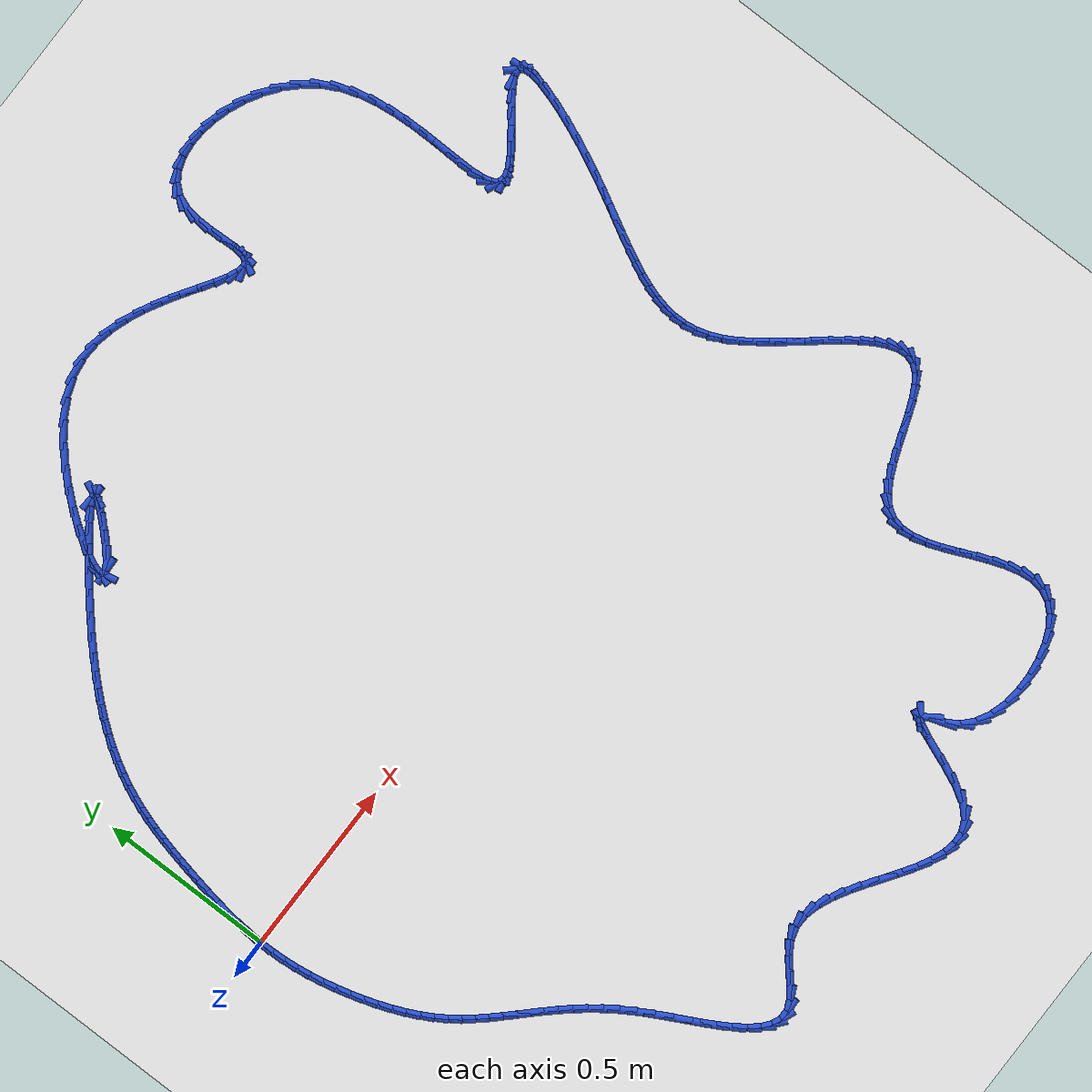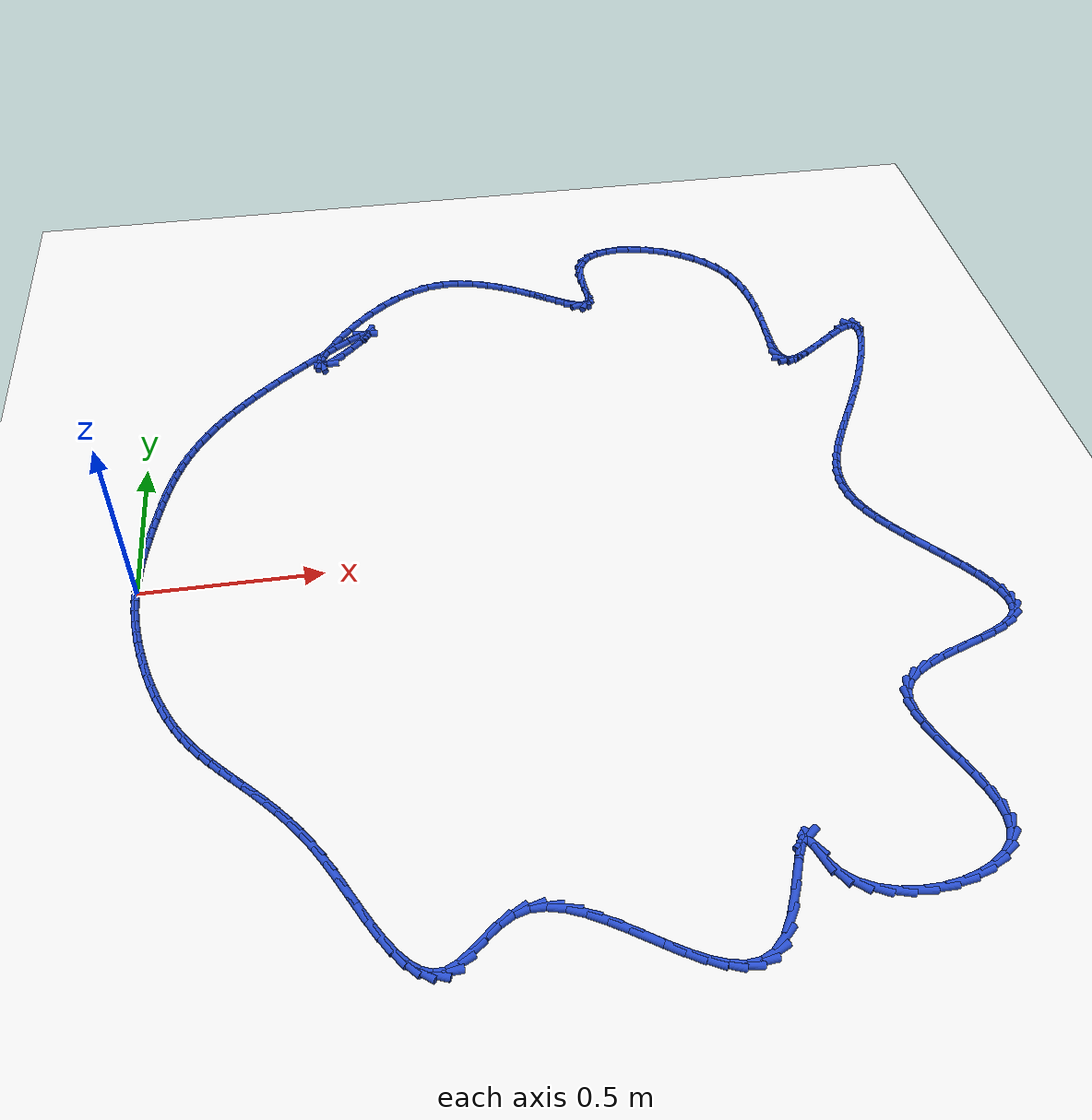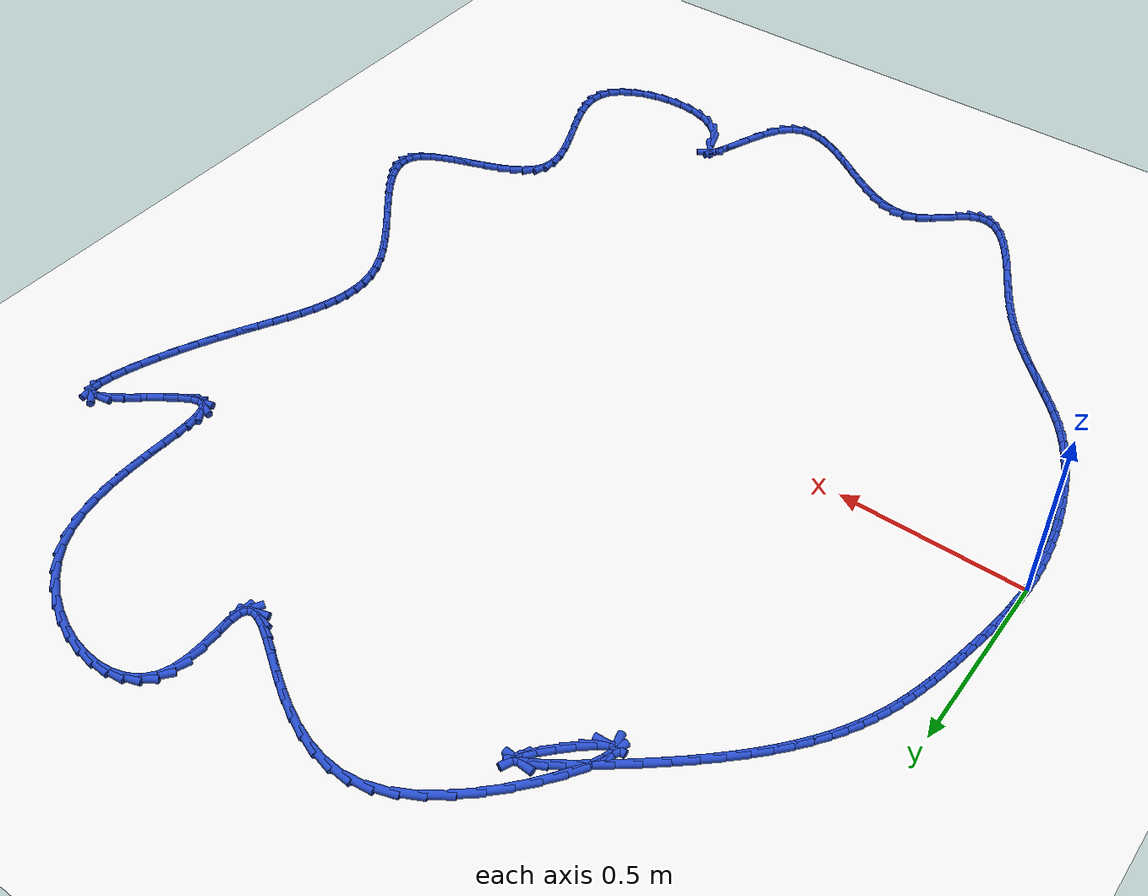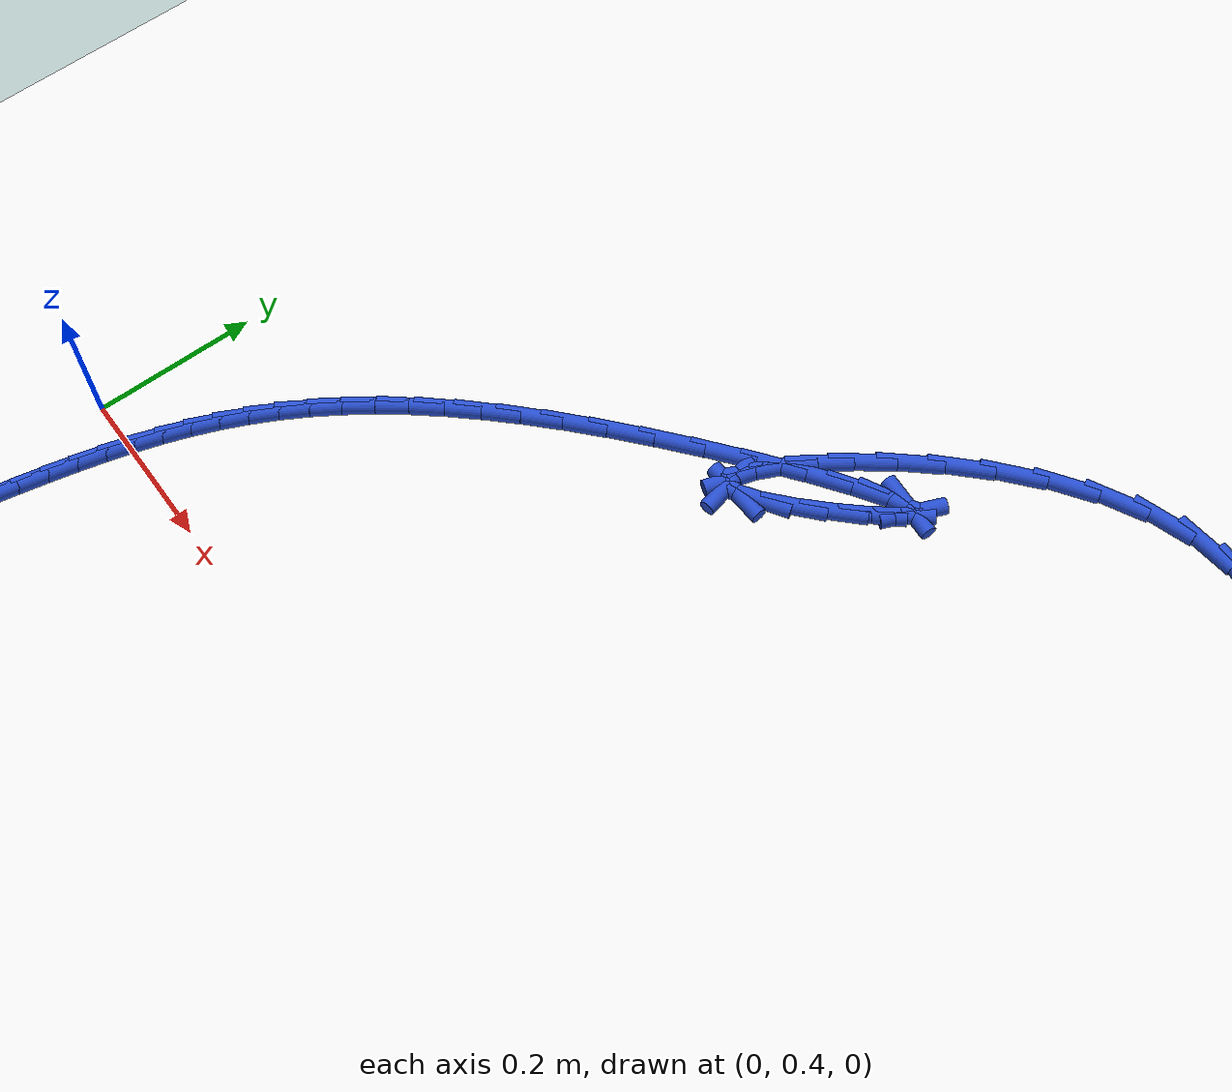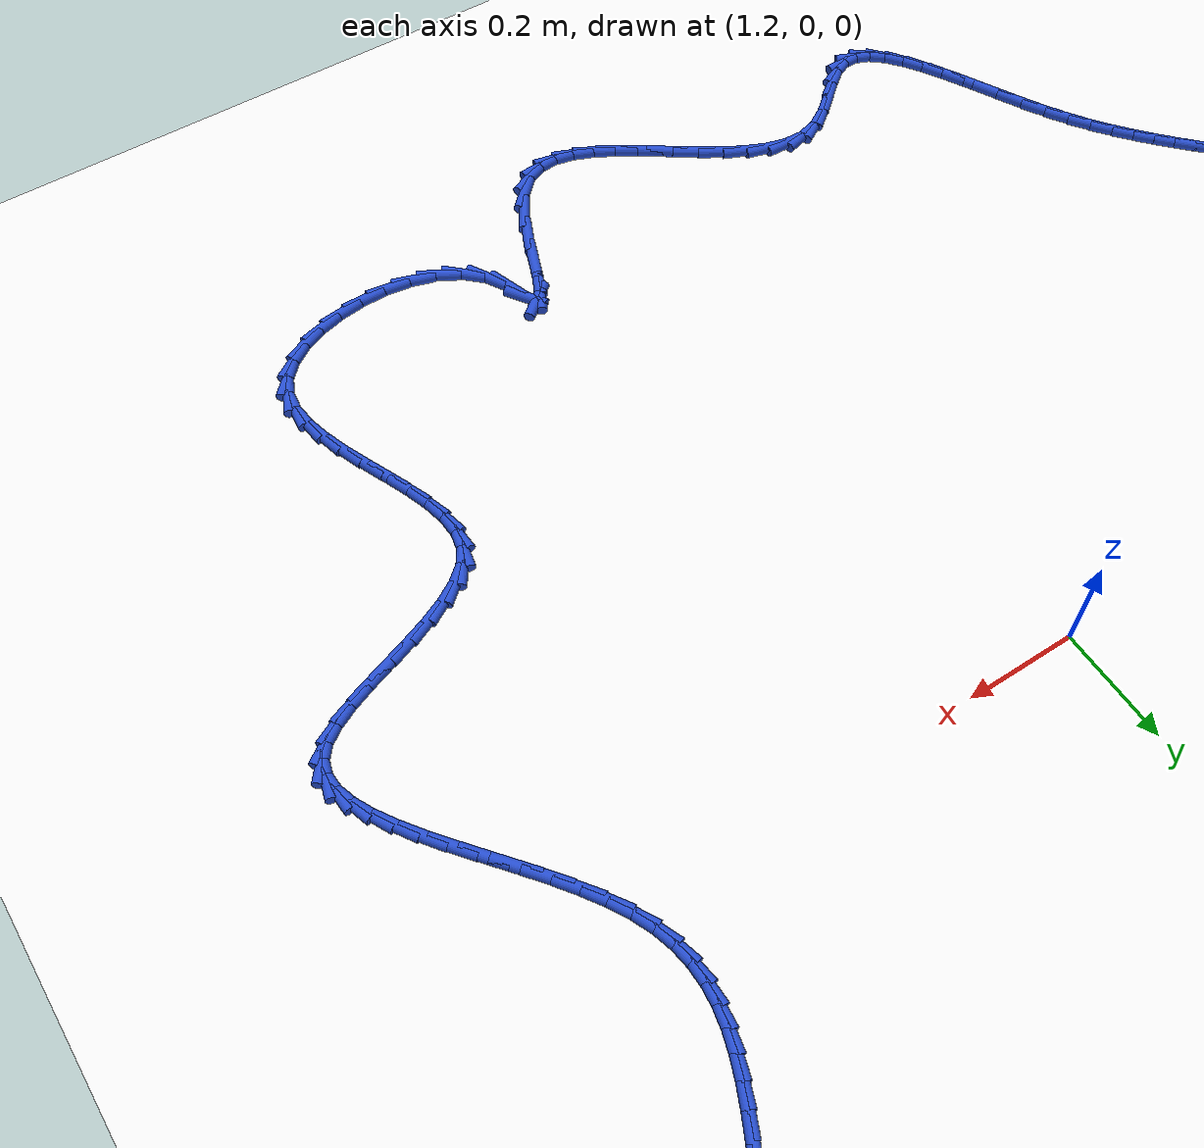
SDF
<sdf version="1.6">
 <world name="default">
  <light name="sun" type="directional">
   <pose>0 0 10 0 -0 0</pose>
   <diffuse>0.8 0.8 0.8 1</diffuse>
   <specular>0.2 0.2 0.2 1</specular>
   <attenuation>
    <range>1000</range>
    <constant>0.9</constant>
    <linear>0.01</linear>
    <quadratic>0.001</quadratic>
   </attenuation>
   <direction>-0.5 0.1 -0.9</direction>
  </light>
  <model name="ground_plane">
   <static>1</static>
   <link name="link">
    <collision name="collision">
     <geometry><plane><normal>0 0 1</normal><size>100 100</size></plane></geometry>
     <surface><friction><ode><mu>100</mu><mu2>50</mu2></ode></friction></surface>
    </collision>
    <visual name="visual">
     <cast_shadows>0</cast_shadows>
     <geometry><plane><normal>0 0 1</normal><size>100 100</size></plane></geometry>
     <material>
      <script><uri>file://media/materials/scripts/gazebo.material</uri><name>Gazebo/WhiteGlow</name></script>
     </material>
    </visual>
   </link>
  </model>
  <gravity>0 0 -9.8</gravity>
  <magnetic_field>6e-06 2.3e-05 -4.2e-05</magnetic_field>
  <atmosphere type="adiabatic"/>
  <physics name="default_physics" default="0" type="ode">
   <max_step_size>0.001</max_step_size>
   <real_time_factor>1</real_time_factor>
   <real_time_update_rate>1000</real_time_update_rate>
  </physics>
  <scene><ambient>0.4 0.4 0.4 1</ambient><background>0.7 0.7 0.7 1</background><shadows>1</shadows></scene>
  <spherical_coordinates>
   <surface_model>EARTH_WGS84</surface_model>
   <latitude_deg>0</latitude_deg>
   <longitude_deg>0</longitude_deg>
   <elevation>0</elevation>
   <heading_deg>0</heading_deg>
  </spherical_coordinates>
  <model name="line">
   <link name="link_0">
    <pose>-1.474514954580286e-17 6.938893903907228e-17 0.01 0 1.57 1.529217470254292</pose>
    <collision name="collision">
     <geometry><cylinder><radius>0.01</radius><length>0.08</length></cylinder></geometry>
    </collision>
    <visual name="visual">
     <material>
      <script><name>Gazebo/Blue</name><uri>file://media/materials/scripts/gazebo.material</uri></script>
     </material>
     <geometry><cylinder><radius>0.01</radius><length>0.08</length></cylinder></geometry>
    </visual>
   </link>
   <link name="link_1">
    <pose>0.0016310443957835209 0.0392051274573912 0.01 0 1.57 1.4876997858208576</pose>
    <collision name="collision">
     <geometry><cylinder><radius>0.01</radius><length>0.08</length></cylinder></geometry>
    </collision>
    <visual name="visual">
     <material>
      <script><name>Gazebo/Blue</name><uri>file://media/materials/scripts/gazebo.material</uri></script>
     </material>
     <geometry><cylinder><radius>0.01</radius><length>0.08</length></cylinder></geometry>
    </visual>
   </link>
   <link name="link_2">
    <pose>0.004903020315258443 0.07849005286956687 0.01 0 1.57 1.4530320091685873</pose>
    <collision name="collision">
     <geometry><cylinder><radius>0.01</radius><length>0.08</length></cylinder></geometry>
    </collision>
    <visual name="visual">
     <material>
      <script><name>Gazebo/Blue</name><uri>file://media/materials/scripts/gazebo.material</uri></script>
     </material>
     <geometry><cylinder><radius>0.01</radius><length>0.08</length></cylinder></geometry>
    </visual>
   </link>
   <link name="link_3">
    <pose>0.009534512002205951 0.11763655705090215 0.01 0 1.57 1.4246528545393173</pose>
    <collision name="collision">
     <geometry><cylinder><radius>0.01</radius><length>0.08</length></cylinder></geometry>
    </collision>
    <visual name="visual">
     <material>
      <script><name>Gazebo/Blue</name><uri>file://media/materials/scripts/gazebo.material</uri></script>
     </material>
     <geometry><cylinder><radius>0.01</radius><length>0.08</length></cylinder></geometry>
    </visual>
   </link>
   <link name="link_4">
    <pose>0.015244103700407232 0.156426420815772 0.01 0 1.57 1.402158840541124</pose>
    <collision name="collision">
     <geometry><cylinder><radius>0.01</radius><length>0.08</length></cylinder></geometry>
    </collision>
    <visual name="visual">
     <material>
      <script><name>Gazebo/Blue</name><uri>file://media/materials/scripts/gazebo.material</uri></script>
     </material>
     <geometry><cylinder><radius>0.01</radius><length>0.08</length></cylinder></geometry>
    </visual>
   </link>
   <link name="link_5">
    <pose>0.021750379653643487 0.19464142497855144 0.01 0 1.57 1.3853210242000125</pose>
    <collision name="collision">
     <geometry><cylinder><radius>0.01</radius><length>0.08</length></cylinder></geometry>
    </collision>
    <visual name="visual">
     <material>
      <script><name>Gazebo/Blue</name><uri>file://media/materials/scripts/gazebo.material</uri></script>
     </material>
     <geometry><cylinder><radius>0.01</radius><length>0.08</length></cylinder></geometry>
    </visual>
   </link>
   <link name="link_6">
    <pose>0.028771924105695915 0.23206335035361553 0.01 0 1.57 1.3740706435438526</pose>
    <collision name="collision">
     <geometry><cylinder><radius>0.01</radius><length>0.08</length></cylinder></geometry>
    </collision>
    <visual name="visual">
     <material>
      <script><name>Gazebo/Blue</name><uri>file://media/materials/scripts/gazebo.material</uri></script>
     </material>
     <geometry><cylinder><radius>0.01</radius><length>0.08</length></cylinder></geometry>
    </visual>
   </link>
   <link name="link_7">
    <pose>0.03602891880428261 0.2684751421928187 0.01 0 1.57 1.36485016169059</pose>
    <collision name="collision">
     <geometry><cylinder><radius>0.01</radius><length>0.08</length></cylinder></geometry>
    </collision>
    <visual name="visual">
     <material>
      <script><name>Gazebo/Blue</name><uri>file://media/materials/scripts/gazebo.material</uri></script>
     </material>
     <geometry><cylinder><radius>0.01</radius><length>0.08</length></cylinder></geometry>
    </visual>
   </link>
   <link name="link_8">
    <pose>0.04340400543061128 0.3037781645081384 0.01 0 1.57 1.3507237780344403</pose>
    <collision name="collision">
     <geometry><cylinder><radius>0.01</radius><length>0.08</length></cylinder></geometry>
    </collision>
    <visual name="visual">
     <material>
      <script><name>Gazebo/Blue</name><uri>file://media/materials/scripts/gazebo.material</uri></script>
     </material>
     <geometry><cylinder><radius>0.01</radius><length>0.08</length></cylinder></geometry>
    </visual>
   </link>
   <link name="link_9">
    <pose>0.051079987475844475 0.33809257242273466 0.01 0 1.57 1.3307526759660895</pose>
    <collision name="collision">
     <geometry><cylinder><radius>0.01</radius><length>0.08</length></cylinder></geometry>
    </collision>
    <visual name="visual">
     <material>
      <script><name>Gazebo/Blue</name><uri>file://media/materials/scripts/gazebo.material</uri></script>
     </material>
     <geometry><cylinder><radius>0.01</radius><length>0.08</length></cylinder></geometry>
    </visual>
   </link>
   <link name="link_10">
    <pose>0.05927210397059078 0.3715621636667952 0.01 0 1.57 1.3049247470604315</pose>
    <collision name="collision">
     <geometry><cylinder><radius>0.01</radius><length>0.08</length></cylinder></geometry>
    </collision>
    <visual name="visual">
     <material>
      <script><name>Gazebo/Blue</name><uri>file://media/materials/scripts/gazebo.material</uri></script>
     </material>
     <geometry><cylinder><radius>0.01</radius><length>0.08</length></cylinder></geometry>
    </visual>
   </link>
   <link name="link_11">
    <pose>0.06819559394545867 0.4043307359705069 0.01 0 1.57 1.2734629107374766</pose>
    <collision name="collision">
     <geometry><cylinder><radius>0.01</radius><length>0.08</length></cylinder></geometry>
    </collision>
    <visual name="visual">
     <material>
      <script><name>Gazebo/Blue</name><uri>file://media/materials/scripts/gazebo.material</uri></script>
     </material>
     <geometry><cylinder><radius>0.01</radius><length>0.08</length></cylinder></geometry>
    </visual>
   </link>
   <link name="link_12">
    <pose>0.07806569643105674 0.43654208706405717 0.01 0 1.57 1.2368506947610896</pose>
    <collision name="collision">
     <geometry><cylinder><radius>0.01</radius><length>0.08</length></cylinder></geometry>
    </collision>
    <visual name="visual">
     <material>
      <script><name>Gazebo/Blue</name><uri>file://media/materials/scripts/gazebo.material</uri></script>
     </material>
     <geometry><cylinder><radius>0.01</radius><length>0.08</length></cylinder></geometry>
    </visual>
   </link>
   <link name="link_13">
    <pose>0.08909765045799348 0.46834001467763303 0.01 0 1.57 1.1958329322564842</pose>
    <collision name="collision">
     <geometry><cylinder><radius>0.01</radius><length>0.08</length></cylinder></geometry>
    </collision>
    <visual name="visual">
     <material>
      <script><name>Gazebo/Blue</name><uri>file://media/materials/scripts/gazebo.material</uri></script>
     </material>
     <geometry><cylinder><radius>0.01</radius><length>0.08</length></cylinder></geometry>
    </visual>
   </link>
   <link name="link_14">
    <pose>0.10150669505687746 0.499868316541422 0.01 0 1.57 1.151383458375795</pose>
    <collision name="collision">
     <geometry><cylinder><radius>0.01</radius><length>0.08</length></cylinder></geometry>
    </collision>
    <visual name="visual">
     <material>
      <script><name>Gazebo/Blue</name><uri>file://media/materials/scripts/gazebo.material</uri></script>
     </material>
     <geometry><cylinder><radius>0.01</radius><length>0.08</length></cylinder></geometry>
    </visual>
   </link>
   <link name="link_15">
    <pose>0.11550806925831719 0.5312707903856111 0.01 0 1.57 1.1046383283907326</pose>
    <collision name="collision">
     <geometry><cylinder><radius>0.01</radius><length>0.08</length></cylinder></geometry>
    </collision>
    <visual name="visual">
     <material>
      <script><name>Gazebo/Blue</name><uri>file://media/materials/scripts/gazebo.material</uri></script>
     </material>
     <geometry><cylinder><radius>0.01</radius><length>0.08</length></cylinder></geometry>
    </visual>
   </link>
   <link name="link_16">
    <pose>0.1313170120929212 0.5626912339403876 0.01 0 1.57 1.056802621539264</pose>
    <collision name="collision">
     <geometry><cylinder><radius>0.01</radius><length>0.08</length></cylinder></geometry>
    </collision>
    <visual name="visual">
     <material>
      <script><name>Gazebo/Blue</name><uri>file://media/materials/scripts/gazebo.material</uri></script>
     </material>
     <geometry><cylinder><radius>0.01</radius><length>0.08</length></cylinder></geometry>
    </visual>
   </link>
   <link name="link_17">
    <pose>0.1491487625912981 0.5942734449359389 0.01 0 1.57 1.0090475129470196</pose>
    <collision name="collision">
     <geometry><cylinder><radius>0.01</radius><length>0.08</length></cylinder></geometry>
    </collision>
    <visual name="visual">
     <material>
      <script><name>Gazebo/Blue</name><uri>file://media/materials/scripts/gazebo.material</uri></script>
     </material>
     <geometry><cylinder><radius>0.01</radius><length>0.08</length></cylinder></geometry>
    </visual>
   </link>
   <link name="link_18">
    <pose>0.16921855978405637 0.6261612211024521 0.01 0 1.57 0.9624176905310876</pose>
    <collision name="collision">
     <geometry><cylinder><radius>0.01</radius><length>0.08</length></cylinder></geometry>
    </collision>
    <visual name="visual">
     <material>
      <script><name>Gazebo/Blue</name><uri>file://media/materials/scripts/gazebo.material</uri></script>
     </material>
     <geometry><cylinder><radius>0.01</radius><length>0.08</length></cylinder></geometry>
    </visual>
   </link>
   <link name="link_19">
    <pose>0.19174164270180455 0.6584983601701142 0.01 0 1.57 0.9177655040409061</pose>
    <collision name="collision">
     <geometry><cylinder><radius>0.01</radius><length>0.08</length></cylinder></geometry>
    </collision>
    <visual name="visual">
     <material>
      <script><name>Gazebo/Blue</name><uri>file://media/materials/scripts/gazebo.material</uri></script>
     </material>
     <geometry><cylinder><radius>0.01</radius><length>0.08</length></cylinder></geometry>
    </visual>
   </link>
   <link name="link_20">
    <pose>0.21693325037515118 0.691428659869113 0.01 0 1.57 0.8757194259328742</pose>
    <collision name="collision">
     <geometry><cylinder><radius>0.01</radius><length>0.08</length></cylinder></geometry>
    </collision>
    <visual name="visual">
     <material>
      <script><name>Gazebo/Blue</name><uri>file://media/materials/scripts/gazebo.material</uri></script>
     </material>
     <geometry><cylinder><radius>0.01</radius><length>0.08</length></cylinder></geometry>
    </visual>
   </link>
   <link name="link_21">
    <pose>0.2450086218347048 0.7250959179296352 0.01 0 1.57 0.8366848180534597</pose>
    <collision name="collision">
     <geometry><cylinder><radius>0.01</radius><length>0.08</length></cylinder></geometry>
    </collision>
    <visual name="visual">
     <material>
      <script><name>Gazebo/Blue</name><uri>file://media/materials/scripts/gazebo.material</uri></script>
     </material>
     <geometry><cylinder><radius>0.01</radius><length>0.08</length></cylinder></geometry>
    </visual>
   </link>
   <link name="link_22">
    <pose>0.276182996111074 0.7596439320818684 0.01 0 1.57 0.8008684325504353</pose>
    <collision name="collision">
     <geometry><cylinder><radius>0.01</radius><length>0.08</length></cylinder></geometry>
    </collision>
    <visual name="visual">
     <material>
      <script><name>Gazebo/Blue</name><uri>file://media/materials/scripts/gazebo.material</uri></script>
     </material>
     <geometry><cylinder><radius>0.01</radius><length>0.08</length></cylinder></geometry>
    </visual>
   </link>
   <link name="link_23">
    <pose>0.3106716122348672 0.7952165000559996 0.01 0 1.57 0.7683158995567205</pose>
    <collision name="collision">
     <geometry><cylinder><radius>0.01</radius><length>0.08</length></cylinder></geometry>
    </collision>
    <visual name="visual">
     <material>
      <script><name>Gazebo/Blue</name><uri>file://media/materials/scripts/gazebo.material</uri></script>
     </material>
     <geometry><cylinder><radius>0.01</radius><length>0.08</length></cylinder></geometry>
    </visual>
   </link>
   <link name="link_24">
    <pose>0.3486897092366932 0.8319574195822164 0.01 0 1.57 0.7389527702259174</pose>
    <collision name="collision">
     <geometry><cylinder><radius>0.01</radius><length>0.08</length></cylinder></geometry>
    </collision>
    <visual name="visual">
     <material>
      <script><name>Gazebo/Blue</name><uri>file://media/materials/scripts/gazebo.material</uri></script>
     </material>
     <geometry><cylinder><radius>0.01</radius><length>0.08</length></cylinder></geometry>
    </visual>
   </link>
   <link name="link_25">
    <pose>0.3904525261471602 0.8700104883907056 0.01 0 1.57 0.713051230423906</pose>
    <collision name="collision">
     <geometry><cylinder><radius>0.01</radius><length>0.08</length></cylinder></geometry>
    </collision>
    <visual name="visual">
     <material>
      <script><name>Gazebo/Blue</name><uri>file://media/materials/scripts/gazebo.material</uri></script>
     </material>
     <geometry><cylinder><radius>0.01</radius><length>0.08</length></cylinder></geometry>
    </visual>
   </link>
   <link name="link_26">
    <pose>0.4358175566111806 0.9092443478881133 0.01 0 1.57 0.691025362570678</pose>
    <collision name="collision">
     <geometry><cylinder><radius>0.01</radius><length>0.08</length></cylinder></geometry>
    </collision>
    <visual name="visual">
     <material>
      <script><name>Gazebo/Blue</name><uri>file://media/materials/scripts/gazebo.material</uri></script>
     </material>
     <geometry><cylinder><radius>0.01</radius><length>0.08</length></cylinder></geometry>
    </visual>
   </link>
   <link name="link_27">
    <pose>0.482954425083118 0.9482294315945302 0.01 0 1.57 0.6702667946903883</pose>
    <collision name="collision">
     <geometry><cylinder><radius>0.01</radius><length>0.08</length></cylinder></geometry>
    </collision>
    <visual name="visual">
     <material>
      <script><name>Gazebo/Blue</name><uri>file://media/materials/scripts/gazebo.material</uri></script>
     </material>
     <geometry><cylinder><radius>0.01</radius><length>0.08</length></cylinder></geometry>
    </visual>
   </link>
   <link name="link_28">
    <pose>0.5295354398446693 0.9851536672167511 0.01 0 1.57 0.6475634134900935</pose>
    <collision name="collision">
     <geometry><cylinder><radius>0.01</radius><length>0.08</length></cylinder></geometry>
    </collision>
    <visual name="visual">
     <material>
      <script><name>Gazebo/Blue</name><uri>file://media/materials/scripts/gazebo.material</uri></script>
     </material>
     <geometry><cylinder><radius>0.01</radius><length>0.08</length></cylinder></geometry>
    </visual>
   </link>
   <link name="link_29">
    <pose>0.5732328388944536 1.0182049284040373 0.01 0 1.57 0.6181152855131918</pose>
    <collision name="collision">
     <geometry><cylinder><radius>0.01</radius><length>0.08</length></cylinder></geometry>
    </collision>
    <visual name="visual">
     <material>
      <script><name>Gazebo/Blue</name><uri>file://media/materials/scripts/gazebo.material</uri></script>
     </material>
     <geometry><cylinder><radius>0.01</radius><length>0.08</length></cylinder></geometry>
    </visual>
   </link>
   <link name="link_30">
    <pose>0.6117188602310893 1.0455710888056489 0.01 0 1.57 0.5707544339160211</pose>
    <collision name="collision">
     <geometry><cylinder><radius>0.01</radius><length>0.08</length></cylinder></geometry>
    </collision>
    <visual name="visual">
     <material>
      <script><name>Gazebo/Blue</name><uri>file://media/materials/scripts/gazebo.material</uri></script>
     </material>
     <geometry><cylinder><radius>0.01</radius><length>0.08</length></cylinder></geometry>
    </visual>
   </link>
   <link name="link_31">
    <pose>0.6426657418531954 1.065440022070847 0.01 0 1.57 0.4643907801852915</pose>
    <collision name="collision">
     <geometry><cylinder><radius>0.01</radius><length>0.08</length></cylinder></geometry>
    </collision>
    <visual name="visual">
     <material>
      <script><name>Gazebo/Blue</name><uri>file://media/materials/scripts/gazebo.material</uri></script>
     </material>
     <geometry><cylinder><radius>0.01</radius><length>0.08</length></cylinder></geometry>
    </visual>
   </link>
   <link name="link_32">
    <pose>0.663745721759391 1.0759996018488929 0.01 0 1.57 -0.06315507419108564</pose>
    <collision name="collision">
     <geometry><cylinder><radius>0.01</radius><length>0.08</length></cylinder></geometry>
    </collision>
    <visual name="visual">
     <material>
      <script><name>Gazebo/Blue</name><uri>file://media/materials/scripts/gazebo.material</uri></script>
     </material>
     <geometry><cylinder><radius>0.01</radius><length>0.08</length></cylinder></geometry>
    </visual>
   </link>
   <link name="link_33">
    <pose>0.6726310379482943 1.0754377017890464 0.01 0 1.57 1.1757035624971568</pose>
    <collision name="collision">
     <geometry><cylinder><radius>0.01</radius><length>0.08</length></cylinder></geometry>
    </collision>
    <visual name="visual">
     <material>
      <script><name>Gazebo/Blue</name><uri>file://media/materials/scripts/gazebo.material</uri></script>
     </material>
     <geometry><cylinder><radius>0.01</radius><length>0.08</length></cylinder></geometry>
    </visual>
   </link>
   <link name="link_34">
    <pose>0.6670097155767161 1.0619579823420613 0.01 0 1.57 0.9104373135603664</pose>
    <collision name="collision">
     <geometry><cylinder><radius>0.01</radius><length>0.08</length></cylinder></geometry>
    </collision>
    <visual name="visual">
     <material>
      <script><name>Gazebo/Blue</name><uri>file://media/materials/scripts/gazebo.material</uri></script>
     </material>
     <geometry><cylinder><radius>0.01</radius><length>0.08</length></cylinder></geometry>
    </visual>
   </link>
   <link name="link_35">
    <pose>0.6469979684740267 1.0361922377680914 0.01 0 1.57 0.8361851049577573</pose>
    <collision name="collision">
     <geometry><cylinder><radius>0.01</radius><length>0.08</length></cylinder></geometry>
    </collision>
    <visual name="visual">
     <material>
      <script><name>Gazebo/Blue</name><uri>file://media/materials/scripts/gazebo.material</uri></script>
     </material>
     <geometry><cylinder><radius>0.01</radius><length>0.08</length></cylinder></geometry>
    </visual>
   </link>
   <link name="link_36">
    <pose>0.6177358901534481 1.0037960285002312 0.01 0 1.57 0.785380018939962</pose>
    <collision name="collision">
     <geometry><cylinder><radius>0.01</radius><length>0.08</length></cylinder></geometry>
    </collision>
    <visual name="visual">
     <material>
      <script><name>Gazebo/Blue</name><uri>file://media/materials/scripts/gazebo.material</uri></script>
     </material>
     <geometry><cylinder><radius>0.01</radius><length>0.08</length></cylinder></geometry>
    </visual>
   </link>
   <link name="link_37">
    <pose>0.5849862254455672 0.971047552220585 0.01 0 1.57 0.721746941263223</pose>
    <collision name="collision">
     <geometry><cylinder><radius>0.01</radius><length>0.08</length></cylinder></geometry>
    </collision>
    <visual name="visual">
     <material>
      <script><name>Gazebo/Blue</name><uri>file://media/materials/scripts/gazebo.material</uri></script>
     </material>
     <geometry><cylinder><radius>0.01</radius><length>0.08</length></cylinder></geometry>
    </visual>
   </link>
   <link name="link_38">
    <pose>0.5545117191809708 0.9442250066112579 0.01 0 1.57 0.5802501104872282</pose>
    <collision name="collision">
     <geometry><cylinder><radius>0.01</radius><length>0.08</length></cylinder></geometry>
    </collision>
    <visual name="visual">
     <material>
      <script><name>Gazebo/Blue</name><uri>file://media/materials/scripts/gazebo.material</uri></script>
     </material>
     <geometry><cylinder><radius>0.01</radius><length>0.08</length></cylinder></geometry>
    </visual>
   </link>
   <link name="link_39">
    <pose>0.5319269630924486 0.9294201123179662 0.01 0 1.57 0.05825708162466657</pose>
    <collision name="collision">
     <geometry><cylinder><radius>0.01</radius><length>0.08</length></cylinder></geometry>
    </collision>
    <visual name="visual">
     <material>
      <script><name>Gazebo/Blue</name><uri>file://media/materials/scripts/gazebo.material</uri></script>
     </material>
     <geometry><cylinder><radius>0.01</radius><length>0.08</length></cylinder></geometry>
    </visual>
   </link>
   <link name="link_40">
    <pose>0.5196524306774435 0.9287042238161648 0.01 0 1.57 -1.3477601561598183</pose>
    <collision name="collision">
     <geometry><cylinder><radius>0.01</radius><length>0.08</length></cylinder></geometry>
    </collision>
    <visual name="visual">
     <material>
      <script><name>Gazebo/Blue</name><uri>file://media/materials/scripts/gazebo.material</uri></script>
     </material>
     <geometry><cylinder><radius>0.01</radius><length>0.08</length></cylinder></geometry>
    </visual>
   </link>
   <link name="link_41">
    <pose>0.5170287198978547 0.9402721241774438 0.01 0 1.57 1.292983288149223</pose>
    <collision name="collision">
     <geometry><cylinder><radius>0.01</radius><length>0.08</length></cylinder></geometry>
    </collision>
    <visual name="visual">
     <material>
      <script><name>Gazebo/Blue</name><uri>file://media/materials/scripts/gazebo.material</uri></script>
     </material>
     <geometry><cylinder><radius>0.01</radius><length>0.08</length></cylinder></geometry>
    </visual>
   </link>
   <link name="link_42">
    <pose>0.5232711336597228 0.9621608903502122 0.01 0 1.57 1.1285178929318345</pose>
    <collision name="collision">
     <geometry><cylinder><radius>0.01</radius><length>0.08</length></cylinder></geometry>
    </collision>
    <visual name="visual">
     <material>
      <script><name>Gazebo/Blue</name><uri>file://media/materials/scripts/gazebo.material</uri></script>
     </material>
     <geometry><cylinder><radius>0.01</radius><length>0.08</length></cylinder></geometry>
    </visual>
   </link>
   <link name="link_43">
    <pose>0.5375949748690882 0.9924075992828795 0.01 0 1.57 1.0377227075274398</pose>
    <collision name="collision">
     <geometry><cylinder><radius>0.01</radius><length>0.08</length></cylinder></geometry>
    </collision>
    <visual name="visual">
     <material>
      <script><name>Gazebo/Blue</name><uri>file://media/materials/scripts/gazebo.material</uri></script>
     </material>
     <geometry><cylinder><radius>0.01</radius><length>0.08</length></cylinder></geometry>
    </visual>
   </link>
   <link name="link_44">
    <pose>0.5592155464319909 1.0290493279238542 0.01 0 1.57 0.9702577181841804</pose>
    <collision name="collision">
     <geometry><cylinder><radius>0.01</radius><length>0.08</length></cylinder></geometry>
    </collision>
    <visual name="visual">
     <material>
      <script><name>Gazebo/Blue</name><uri>file://media/materials/scripts/gazebo.material</uri></script>
     </material>
     <geometry><cylinder><radius>0.01</radius><length>0.08</length></cylinder></geometry>
    </visual>
   </link>
   <link name="link_45">
    <pose>0.5873481512544718 1.070123153221546 0.01 0 1.57 0.9098509839630275</pose>
    <collision name="collision">
     <geometry><cylinder><radius>0.01</radius><length>0.08</length></cylinder></geometry>
    </collision>
    <visual name="visual">
     <material>
      <script><name>Gazebo/Blue</name><uri>file://media/materials/scripts/gazebo.material</uri></script>
     </material>
     <geometry><cylinder><radius>0.01</radius><length>0.08</length></cylinder></geometry>
    </visual>
   </link>
   <link name="link_46">
    <pose>0.6212080922425705 1.1136661521243638 0.01 0 1.57 0.8486396500593082</pose>
    <collision name="collision">
     <geometry><cylinder><radius>0.01</radius><length>0.08</length></cylinder></geometry>
    </collision>
    <visual name="visual">
     <material>
      <script><name>Gazebo/Blue</name><uri>file://media/materials/scripts/gazebo.material</uri></script>
     </material>
     <geometry><cylinder><radius>0.01</radius><length>0.08</length></cylinder></geometry>
    </visual>
   </link>
   <link name="link_47">
    <pose>0.6600106723023277 1.1577154015807163 0.01 0 1.57 0.781097409656063</pose>
    <collision name="collision">
     <geometry><cylinder><radius>0.01</radius><length>0.08</length></cylinder></geometry>
    </collision>
    <visual name="visual">
     <material>
      <script><name>Gazebo/Blue</name><uri>file://media/materials/scripts/gazebo.material</uri></script>
     </material>
     <geometry><cylinder><radius>0.01</radius><length>0.08</length></cylinder></geometry>
    </visual>
   </link>
   <link name="link_48">
    <pose>0.7029711943397837 1.2003079785390132 0.01 0 1.57 0.7018478522293659</pose>
    <collision name="collision">
     <geometry><cylinder><radius>0.01</radius><length>0.08</length></cylinder></geometry>
    </collision>
    <visual name="visual">
     <material>
      <script><name>Gazebo/Blue</name><uri>file://media/materials/scripts/gazebo.material</uri></script>
     </material>
     <geometry><cylinder><radius>0.01</radius><length>0.08</length></cylinder></geometry>
    </visual>
   </link>
   <link name="link_49">
    <pose>0.7493049612609786 1.2394809599476633 0.01 0 1.57 0.6044545552586118</pose>
    <collision name="collision">
     <geometry><cylinder><radius>0.01</radius><length>0.08</length></cylinder></geometry>
    </collision>
    <visual name="visual">
     <material>
      <script><name>Gazebo/Blue</name><uri>file://media/materials/scripts/gazebo.material</uri></script>
     </material>
     <geometry><cylinder><radius>0.01</radius><length>0.08</length></cylinder></geometry>
    </visual>
   </link>
   <link name="link_50">
    <pose>0.7982272759719531 1.2732714227550757 0.01 0 1.57 0.4805648511193775</pose>
    <collision name="collision">
     <geometry><cylinder><radius>0.01</radius><length>0.08</length></cylinder></geometry>
    </collision>
    <visual name="visual">
     <material>
      <script><name>Gazebo/Blue</name><uri>file://media/materials/scripts/gazebo.material</uri></script>
     </material>
     <geometry><cylinder><radius>0.01</radius><length>0.08</length></cylinder></geometry>
    </visual>
   </link>
   <link name="link_51">
    <pose>0.8489534413787472 1.2997164439096598 0.01 0 1.57 0.3198050641687751</pose>
    <collision name="collision">
     <geometry><cylinder><radius>0.01</radius><length>0.08</length></cylinder></geometry>
    </collision>
    <visual name="visual">
     <material>
      <script><name>Gazebo/Blue</name><uri>file://media/materials/scripts/gazebo.material</uri></script>
     </material>
     <geometry><cylinder><radius>0.01</radius><length>0.08</length></cylinder></geometry>
    </visual>
   </link>
   <link name="link_52">
    <pose>0.900698760387401 1.3168531003598238 0.01 0 1.57 0.12111255086555098</pose>
    <collision name="collision">
     <geometry><cylinder><radius>0.01</radius><length>0.08</length></cylinder></geometry>
    </collision>
    <visual name="visual">
     <material>
      <script><name>Gazebo/Blue</name><uri>file://media/materials/scripts/gazebo.material</uri></script>
     </material>
     <geometry><cylinder><radius>0.01</radius><length>0.08</length></cylinder></geometry>
    </visual>
   </link>
   <link name="link_53">
    <pose>0.9527135433864252 1.323183726792735 0.01 0 1.57 -0.0678575687497394</pose>
    <collision name="collision">
     <geometry><cylinder><radius>0.01</radius><length>0.08</length></cylinder></geometry>
    </collision>
    <visual name="visual">
     <material>
      <script><name>Gazebo/Blue</name><uri>file://media/materials/scripts/gazebo.material</uri></script>
     </material>
     <geometry><cylinder><radius>0.01</radius><length>0.08</length></cylinder></geometry>
    </visual>
   </link>
   <link name="link_54">
    <pose>1.004433056965143 1.3196687696387563 0.01 0 1.57 -0.22382158209609068</pose>
    <collision name="collision">
     <geometry><cylinder><radius>0.01</radius><length>0.08</length></cylinder></geometry>
    </collision>
    <visual name="visual">
     <material>
      <script><name>Gazebo/Blue</name><uri>file://media/materials/scripts/gazebo.material</uri></script>
     </material>
     <geometry><cylinder><radius>0.01</radius><length>0.08</length></cylinder></geometry>
    </visual>
   </link>
   <link name="link_55">
    <pose>1.055353425018829 1.3080774833474578 0.01 0 1.57 -0.34619085383143294</pose>
    <collision name="collision">
     <geometry><cylinder><radius>0.01</radius><length>0.08</length></cylinder></geometry>
    </collision>
    <visual name="visual">
     <material>
      <script><name>Gazebo/Blue</name><uri>file://media/materials/scripts/gazebo.material</uri></script>
     </material>
     <geometry><cylinder><radius>0.01</radius><length>0.08</length></cylinder></geometry>
    </visual>
   </link>
   <link name="link_56">
    <pose>1.1049708082517349 1.2901796115684312 0.01 0 1.57 -0.4387397024534806</pose>
    <collision name="collision">
     <geometry><cylinder><radius>0.01</radius><length>0.08</length></cylinder></geometry>
    </collision>
    <visual name="visual">
     <material>
      <script><name>Gazebo/Blue</name><uri>file://media/materials/scripts/gazebo.material</uri></script>
     </material>
     <geometry><cylinder><radius>0.01</radius><length>0.08</length></cylinder></geometry>
    </visual>
   </link>
   <link name="link_57">
    <pose>1.1527813673681118 1.2677448979512675 0.01 0 1.57 -0.5058227592215292</pose>
    <collision name="collision">
     <geometry><cylinder><radius>0.01</radius><length>0.08</length></cylinder></geometry>
    </collision>
    <visual name="visual">
     <material>
      <script><name>Gazebo/Blue</name><uri>file://media/materials/scripts/gazebo.material</uri></script>
     </material>
     <geometry><cylinder><radius>0.01</radius><length>0.08</length></cylinder></geometry>
    </visual>
   </link>
   <link name="link_58">
    <pose>1.1982812630722113 1.242543086145558 0.01 0 1.57 -0.550485620778103</pose>
    <collision name="collision">
     <geometry><cylinder><radius>0.01</radius><length>0.08</length></cylinder></geometry>
    </collision>
    <visual name="visual">
     <material>
      <script><name>Gazebo/Blue</name><uri>file://media/materials/scripts/gazebo.material</uri></script>
     </material>
     <geometry><cylinder><radius>0.01</radius><length>0.08</length></cylinder></geometry>
    </visual>
   </link>
   <link name="link_59">
    <pose>1.2409666560682844 1.216343919800894 0.01 0 1.57 -0.5734803814604125</pose>
    <collision name="collision">
     <geometry><cylinder><radius>0.01</radius><length>0.08</length></cylinder></geometry>
    </collision>
    <visual name="visual">
     <material>
      <script><name>Gazebo/Blue</name><uri>file://media/materials/scripts/gazebo.material</uri></script>
     </material>
     <geometry><cylinder><radius>0.01</radius><length>0.08</length></cylinder></geometry>
    </visual>
   </link>
   <link name="link_60">
    <pose>1.2803337070605834 1.1909171425668676 0.01 0 1.57 -0.5720213942434541</pose>
    <collision name="collision">
     <geometry><cylinder><radius>0.01</radius><length>0.08</length></cylinder></geometry>
    </collision>
    <visual name="visual">
     <material>
      <script><name>Gazebo/Blue</name><uri>file://media/materials/scripts/gazebo.material</uri></script>
     </material>
     <geometry><cylinder><radius>0.01</radius><length>0.08</length></cylinder></geometry>
    </visual>
   </link>
   <link name="link_61">
    <pose>1.3158785767533585 1.1680324980930696 0.01 0 1.57 -0.5366770247992301</pose>
    <collision name="collision">
     <geometry><cylinder><radius>0.01</radius><length>0.08</length></cylinder></geometry>
    </collision>
    <visual name="visual">
     <material>
      <script><name>Gazebo/Blue</name><uri>file://media/materials/scripts/gazebo.material</uri></script>
     </material>
     <geometry><cylinder><radius>0.01</radius><length>0.08</length></cylinder></geometry>
    </visual>
   </link>
   <link name="link_62">
    <pose>1.3470974258508621 1.1494597300290916 0.01 0 1.57 -0.4420987461079205</pose>
    <collision name="collision">
     <geometry><cylinder><radius>0.01</radius><length>0.08</length></cylinder></geometry>
    </collision>
    <visual name="visual">
     <material>
      <script><name>Gazebo/Blue</name><uri>file://media/materials/scripts/gazebo.material</uri></script>
     </material>
     <geometry><cylinder><radius>0.01</radius><length>0.08</length></cylinder></geometry>
    </visual>
   </link>
   <link name="link_63">
    <pose>1.3734864150573458 1.1369685820245248 0.01 0 1.57 -0.2168954977751172</pose>
    <collision name="collision">
     <geometry><cylinder><radius>0.01</radius><length>0.08</length></cylinder></geometry>
    </collision>
    <visual name="visual">
     <material>
      <script><name>Gazebo/Blue</name><uri>file://media/materials/scripts/gazebo.material</uri></script>
     </material>
     <geometry><cylinder><radius>0.01</radius><length>0.08</length></cylinder></geometry>
    </visual>
   </link>
   <link name="link_64">
    <pose>1.3945417050770597 1.1323287977289607 0.01 0 1.57 0.3163435836537998</pose>
    <collision name="collision">
     <geometry><cylinder><radius>0.01</radius><length>0.08</length></cylinder></geometry>
    </collision>
    <visual name="visual">
     <material>
      <script><name>Gazebo/Blue</name><uri>file://media/materials/scripts/gazebo.material</uri></script>
     </material>
     <geometry><cylinder><radius>0.01</radius><length>0.08</length></cylinder></geometry>
    </visual>
   </link>
   <link name="link_65">
    <pose>1.4097594566142557 1.1373101207919902 0.01 0 1.57 1.073990398935057</pose>
    <collision name="collision">
     <geometry><cylinder><radius>0.01</radius><length>0.08</length></cylinder></geometry>
    </collision>
    <visual name="visual">
     <material>
      <script><name>Gazebo/Blue</name><uri>file://media/materials/scripts/gazebo.material</uri></script>
     </material>
     <geometry><cylinder><radius>0.01</radius><length>0.08</length></cylinder></geometry>
    </visual>
   </link>
   <link name="link_66">
    <pose>1.4186358319287273 1.1536822923600076 0.01 0 1.57 1.4782395024272896</pose>
    <collision name="collision">
     <geometry><cylinder><radius>0.01</radius><length>0.08</length></cylinder></geometry>
    </collision>
    <visual name="visual">
     <material>
      <script><name>Gazebo/Blue</name><uri>file://media/materials/scripts/gazebo.material</uri></script>
     </material>
     <geometry><cylinder><radius>0.01</radius><length>0.08</length></cylinder></geometry>
    </visual>
   </link>
   <link name="link_67">
    <pose>1.4212848355850025 1.1822208132741445 0.01 0 1.57 -1.5417814878944056</pose>
    <collision name="collision">
     <geometry><cylinder><radius>0.01</radius><length>0.08</length></cylinder></geometry>
    </collision>
    <visual name="visual">
     <material>
      <script><name>Gazebo/Blue</name><uri>file://media/materials/scripts/gazebo.material</uri></script>
     </material>
     <geometry><cylinder><radius>0.01</radius><length>0.08</length></cylinder></geometry>
    </visual>
   </link>
   <link name="link_68">
    <pose>1.420191697594676 1.2198853758848303 0.01 0 1.57 -1.5292357707222544</pose>
    <collision name="collision">
     <geometry><cylinder><radius>0.01</radius><length>0.08</length></cylinder></geometry>
    </collision>
    <visual name="visual">
     <material>
      <script><name>Gazebo/Blue</name><uri>file://media/materials/scripts/gazebo.material</uri></script>
     </material>
     <geometry><cylinder><radius>0.01</radius><length>0.08</length></cylinder></geometry>
    </visual>
   </link>
   <link name="link_69">
    <pose>1.4184104249326042 1.2627203888572482 0.01 0 1.57 1.5575257928130686</pose>
    <collision name="collision">
     <geometry><cylinder><radius>0.01</radius><length>0.08</length></cylinder></geometry>
    </collision>
    <visual name="visual">
     <material>
      <script><name>Gazebo/Blue</name><uri>file://media/materials/scripts/gazebo.material</uri></script>
     </material>
     <geometry><cylinder><radius>0.01</radius><length>0.08</length></cylinder></geometry>
    </visual>
   </link>
   <link name="link_70">
    <pose>1.4189950245736465 1.3067702608565814 0.01 0 1.57 1.4264524954980144</pose>
    <collision name="collision">
     <geometry><cylinder><radius>0.01</radius><length>0.08</length></cylinder></geometry>
    </collision>
    <visual name="visual">
     <material>
      <script><name>Gazebo/Blue</name><uri>file://media/materials/scripts/gazebo.material</uri></script>
     </material>
     <geometry><cylinder><radius>0.01</radius><length>0.08</length></cylinder></geometry>
    </visual>
   </link>
   <link name="link_71">
    <pose>1.4249995034926581 1.3480794005480115 0.01 0 1.57 1.1809414222038175</pose>
    <collision name="collision">
     <geometry><cylinder><radius>0.01</radius><length>0.08</length></cylinder></geometry>
    </collision>
    <visual name="visual">
     <material>
      <script><name>Gazebo/Blue</name><uri>file://media/materials/scripts/gazebo.material</uri></script>
     </material>
     <geometry><cylinder><radius>0.01</radius><length>0.08</length></cylinder></geometry>
    </visual>
   </link>
   <link name="link_72">
    <pose>1.4392941006625046 1.3828691501328971 0.01 0 1.57 0.8620911882032548</pose>
    <collision name="collision">
     <geometry><cylinder><radius>0.01</radius><length>0.08</length></cylinder></geometry>
    </collision>
    <visual name="visual">
     <material>
      <script><name>Gazebo/Blue</name><uri>file://media/materials/scripts/gazebo.material</uri></script>
     </material>
     <geometry><cylinder><radius>0.01</radius><length>0.08</length></cylinder></geometry>
    </visual>
   </link>
   <link name="link_73">
    <pose>1.462306453932633 1.4097126108214784 0.01 0 1.57 0.5615721198788256</pose>
    <collision name="collision">
     <geometry><cylinder><radius>0.01</radius><length>0.08</length></cylinder></geometry>
    </collision>
    <visual name="visual">
     <material>
      <script><name>Gazebo/Blue</name><uri>file://media/materials/scripts/gazebo.material</uri></script>
     </material>
     <geometry><cylinder><radius>0.01</radius><length>0.08</length></cylinder></geometry>
    </visual>
   </link>
   <link name="link_74">
    <pose>1.4927295317153917 1.4288530396415071 0.01 0 1.57 0.31068465095912756</pose>
    <collision name="collision">
     <geometry><cylinder><radius>0.01</radius><length>0.08</length></cylinder></geometry>
    </collision>
    <visual name="visual">
     <material>
      <script><name>Gazebo/Blue</name><uri>file://media/materials/scripts/gazebo.material</uri></script>
     </material>
     <geometry><cylinder><radius>0.01</radius><length>0.08</length></cylinder></geometry>
    </visual>
   </link>
   <link name="link_75">
    <pose>1.529219340147345 1.4405692812425621 0.01 0 1.57 0.11045893317691098</pose>
    <collision name="collision">
     <geometry><cylinder><radius>0.01</radius><length>0.08</length></cylinder></geometry>
    </collision>
    <visual name="visual">
     <material>
      <script><name>Gazebo/Blue</name><uri>file://media/materials/scripts/gazebo.material</uri></script>
     </material>
     <geometry><cylinder><radius>0.01</radius><length>0.08</length></cylinder></geometry>
    </visual>
   </link>
   <link name="link_76">
    <pose>1.5704318853650607 1.4451401802742232 0.01 0 1.57 -0.05143547558953934</pose>
    <collision name="collision">
     <geometry><cylinder><radius>0.01</radius><length>0.08</length></cylinder></geometry>
    </collision>
    <visual name="visual">
     <material>
      <script><name>Gazebo/Blue</name><uri>file://media/materials/scripts/gazebo.material</uri></script>
     </material>
     <geometry><cylinder><radius>0.01</radius><length>0.08</length></cylinder></geometry>
    </visual>
   </link>
   <link name="link_77">
    <pose>1.6150231735051037 1.4428445813860702 0.01 0 1.57 -0.1882650131491371</pose>
    <collision name="collision">
     <geometry><cylinder><radius>0.01</radius><length>0.08</length></cylinder></geometry>
    </collision>
    <visual name="visual">
     <material>
      <script><name>Gazebo/Blue</name><uri>file://media/materials/scripts/gazebo.material</uri></script>
     </material>
     <geometry><cylinder><radius>0.01</radius><length>0.08</length></cylinder></geometry>
    </visual>
   </link>
   <link name="link_78">
    <pose>1.6616492107040415 1.4339613292276818 0.01 0 1.57 -0.3106743683656317</pose>
    <collision name="collision">
     <geometry><cylinder><radius>0.01</radius><length>0.08</length></cylinder></geometry>
    </collision>
    <visual name="visual">
     <material>
      <script><name>Gazebo/Blue</name><uri>file://media/materials/scripts/gazebo.material</uri></script>
     </material>
     <geometry><cylinder><radius>0.01</radius><length>0.08</length></cylinder></geometry>
    </visual>
   </link>
   <link name="link_79">
    <pose>1.7089660030984388 1.4187692684486382 0.01 0 1.57 -0.4268284969456083</pose>
    <collision name="collision">
     <geometry><cylinder><radius>0.01</radius><length>0.08</length></cylinder></geometry>
    </collision>
    <visual name="visual">
     <material>
      <script><name>Gazebo/Blue</name><uri>file://media/materials/scripts/gazebo.material</uri></script>
     </material>
     <geometry><cylinder><radius>0.01</radius><length>0.08</length></cylinder></geometry>
    </visual>
   </link>
   <link name="link_80">
    <pose>1.7556295568248619 1.3975472436985188 0.01 0 1.57 -0.5432683136498143</pose>
    <collision name="collision">
     <geometry><cylinder><radius>0.01</radius><length>0.08</length></cylinder></geometry>
    </collision>
    <visual name="visual">
     <material>
      <script><name>Gazebo/Blue</name><uri>file://media/materials/scripts/gazebo.material</uri></script>
     </material>
     <geometry><cylinder><radius>0.01</radius><length>0.08</length></cylinder></geometry>
    </visual>
   </link>
   <link name="link_81">
    <pose>1.8002958780198786 1.3705740996269025 0.01 0 1.57 -0.6656055834820161</pose>
    <collision name="collision">
     <geometry><cylinder><radius>0.01</radius><length>0.08</length></cylinder></geometry>
    </collision>
    <visual name="visual">
     <material>
      <script><name>Gazebo/Blue</name><uri>file://media/materials/scripts/gazebo.material</uri></script>
     </material>
     <geometry><cylinder><radius>0.01</radius><length>0.08</length></cylinder></geometry>
    </visual>
   </link>
   <link name="link_82">
    <pose>1.841620972820053 1.3381286808833697 0.01 0 1.57 -0.7988463482347915</pose>
    <collision name="collision">
     <geometry><cylinder><radius>0.01</radius><length>0.08</length></cylinder></geometry>
    </collision>
    <visual name="visual">
     <material>
      <script><name>Gazebo/Blue</name><uri>file://media/materials/scripts/gazebo.material</uri></script>
     </material>
     <geometry><cylinder><radius>0.01</radius><length>0.08</length></cylinder></geometry>
    </visual>
   </link>
   <link name="link_83">
    <pose>1.8782608473619522 1.3004898321174996 0.01 0 1.57 -0.9472038485041745</pose>
    <collision name="collision">
     <geometry><cylinder><radius>0.01</radius><length>0.08</length></cylinder></geometry>
    </collision>
    <visual name="visual">
     <material>
      <script><name>Gazebo/Blue</name><uri>file://media/materials/scripts/gazebo.material</uri></script>
     </material>
     <geometry><cylinder><radius>0.01</radius><length>0.08</length></cylinder></geometry>
    </visual>
   </link>
   <link name="link_84">
    <pose>1.9088715077821419 1.2579363979788716 0.01 0 1.57 -1.110380265226519</pose>
    <collision name="collision">
     <geometry><cylinder><radius>0.01</radius><length>0.08</length></cylinder></geometry>
    </collision>
    <visual name="visual">
     <material>
      <script><name>Gazebo/Blue</name><uri>file://media/materials/scripts/gazebo.material</uri></script>
     </material>
     <geometry><cylinder><radius>0.01</radius><length>0.08</length></cylinder></geometry>
    </visual>
   </link>
   <link name="link_85">
    <pose>1.932248152015312 1.210802937427662 0.01 0 1.57 -1.2582279417803577</pose>
    <collision name="collision">
     <geometry><cylinder><radius>0.01</radius><length>0.08</length></cylinder></geometry>
    </collision>
    <visual name="visual">
     <material>
      <script><name>Gazebo/Blue</name><uri>file://media/materials/scripts/gazebo.material</uri></script>
     </material>
     <geometry><cylinder><radius>0.01</radius><length>0.08</length></cylinder></geometry>
    </visual>
   </link>
   <link name="link_86">
    <pose>1.9486610533721995 1.160014437946167 0.01 0 1.57 -1.3738588940804595</pose>
    <collision name="collision">
     <geometry><cylinder><radius>0.01</radius><length>0.08</length></cylinder></geometry>
    </collision>
    <visual name="visual">
     <material>
      <script><name>Gazebo/Blue</name><uri>file://media/materials/scripts/gazebo.material</uri></script>
     </material>
     <geometry><cylinder><radius>0.01</radius><length>0.08</length></cylinder></geometry>
    </visual>
   </link>
   <link name="link_87">
    <pose>1.9592683583575459 1.106851276081046 0.01 0 1.57 -1.4611593790795754</pose>
    <collision name="collision">
     <geometry><cylinder><radius>0.01</radius><length>0.08</length></cylinder></geometry>
    </collision>
    <visual name="visual">
     <material>
      <script><name>Gazebo/Blue</name><uri>file://media/materials/scripts/gazebo.material</uri></script>
     </material>
     <geometry><cylinder><radius>0.01</radius><length>0.08</length></cylinder></geometry>
    </visual>
   </link>
   <link name="link_88">
    <pose>1.9652403925103799 1.0525987032818498 0.01 0 1.57 -1.524450691581582</pose>
    <collision name="collision">
     <geometry><cylinder><radius>0.01</radius><length>0.08</length></cylinder></geometry>
    </collision>
    <visual name="visual">
     <material>
      <script><name>Gazebo/Blue</name><uri>file://media/materials/scripts/gazebo.material</uri></script>
     </material>
     <geometry><cylinder><radius>0.01</radius><length>0.08</length></cylinder></geometry>
    </visual>
   </link>
   <link name="link_89">
    <pose>1.9677474813697282 0.9985419709981278 0.01 0 1.57 -1.5667551406680393</pose>
    <collision name="collision">
     <geometry><cylinder><radius>0.01</radius><length>0.08</length></cylinder></geometry>
    </collision>
    <visual name="visual">
     <material>
      <script><name>Gazebo/Blue</name><uri>file://media/materials/scripts/gazebo.material</uri></script>
     </material>
     <geometry><cylinder><radius>0.01</radius><length>0.08</length></cylinder></geometry>
    </visual>
   </link>
   <link name="link_90">
    <pose>1.9679599504746201 0.9459663306794324 0.01 0 1.57 1.5524920476686033</pose>
    <collision name="collision">
     <geometry><cylinder><radius>0.01</radius><length>0.08</length></cylinder></geometry>
    </collision>
    <visual name="visual">
     <material>
      <script><name>Gazebo/Blue</name><uri>file://media/materials/scripts/gazebo.material</uri></script>
     </material>
     <geometry><cylinder><radius>0.01</radius><length>0.08</length></cylinder></geometry>
    </visual>
   </link>
   <link name="link_91">
    <pose>1.9670481253640832 0.896157033775314 0.01 0 1.57 1.551877315386698</pose>
    <collision name="collision">
     <geometry><cylinder><radius>0.01</radius><length>0.08</length></cylinder></geometry>
    </collision>
    <visual name="visual">
     <material>
      <script><name>Gazebo/Blue</name><uri>file://media/materials/scripts/gazebo.material</uri></script>
     </material>
     <geometry><cylinder><radius>0.01</radius><length>0.08</length></cylinder></geometry>
    </visual>
   </link>
   <link name="link_92">
    <pose>1.9661823315771447 0.8503993317353225 0.01 0 1.57 -1.5621237175627367</pose>
    <collision name="collision">
     <geometry><cylinder><radius>0.01</radius><length>0.08</length></cylinder></geometry>
    </collision>
    <visual name="visual">
     <material>
      <script><name>Gazebo/Blue</name><uri>file://media/materials/scripts/gazebo.material</uri></script>
     </material>
     <geometry><cylinder><radius>0.01</radius><length>0.08</length></cylinder></geometry>
    </visual>
   </link>
   <link name="link_93">
    <pose>1.966532894652834 0.8099784760090086 0.01 0 1.57 -1.489986122174242</pose>
    <collision name="collision">
     <geometry><cylinder><radius>0.01</radius><length>0.08</length></cylinder></geometry>
    </collision>
    <visual name="visual">
     <material>
      <script><name>Gazebo/Blue</name><uri>file://media/materials/scripts/gazebo.material</uri></script>
     </material>
     <geometry><cylinder><radius>0.01</radius><length>0.08</length></cylinder></geometry>
    </visual>
   </link>
   <link name="link_94">
    <pose>1.9692701401301786 0.7761797180459242 0.01 0 1.57 -1.3323203555880963</pose>
    <collision name="collision">
     <geometry><cylinder><radius>0.01</radius><length>0.08</length></cylinder></geometry>
    </collision>
    <visual name="visual">
     <material>
      <script><name>Gazebo/Blue</name><uri>file://media/materials/scripts/gazebo.material</uri></script>
     </material>
     <geometry><cylinder><radius>0.01</radius><length>0.08</length></cylinder></geometry>
    </visual>
   </link>
   <link name="link_95">
    <pose>1.9755643935482072 0.7502883092956194 0.01 0 1.57 -0.9874077373202598</pose>
    <collision name="collision">
     <geometry><cylinder><radius>0.01</radius><length>0.08</length></cylinder></geometry>
    </collision>
    <visual name="visual">
     <material>
      <script><name>Gazebo/Blue</name><uri>file://media/materials/scripts/gazebo.material</uri></script>
     </material>
     <geometry><cylinder><radius>0.01</radius><length>0.08</length></cylinder></geometry>
    </visual>
   </link>
   <link name="link_96">
    <pose>1.9865859804459465 0.7335895012076443 0.01 0 1.57 -0.3523423061189216</pose>
    <collision name="collision">
     <geometry><cylinder><radius>0.01</radius><length>0.08</length></cylinder></geometry>
    </collision>
    <visual name="visual">
     <material>
      <script><name>Gazebo/Blue</name><uri>file://media/materials/scripts/gazebo.material</uri></script>
     </material>
     <geometry><cylinder><radius>0.01</radius><length>0.08</length></cylinder></geometry>
    </visual>
   </link>
   <link name="link_97">
    <pose>2.003505226362426 0.7273685452315507 0.01 0 1.57 0.22686735148599937</pose>
    <collision name="collision">
     <geometry><cylinder><radius>0.01</radius><length>0.08</length></cylinder></geometry>
    </collision>
    <visual name="visual">
     <material>
      <script><name>Gazebo/Blue</name><uri>file://media/materials/scripts/gazebo.material</uri></script>
     </material>
     <geometry><cylinder><radius>0.01</radius><length>0.08</length></cylinder></geometry>
    </visual>
   </link>
   <link name="link_98">
    <pose>2.027488308505057 0.732904833092843 0.01 0 1.57 0.5017308571314343</pose>
    <collision name="collision">
     <geometry><cylinder><radius>0.01</radius><length>0.08</length></cylinder></geometry>
    </collision>
    <visual name="visual">
     <material>
      <script><name>Gazebo/Blue</name><uri>file://media/materials/scripts/gazebo.material</uri></script>
     </material>
     <geometry><cylinder><radius>0.01</radius><length>0.08</length></cylinder></geometry>
    </visual>
   </link>
   <link name="link_99">
    <pose>2.0586569983275576 0.7500024816173153 0.01 0 1.57 0.6071374303865636</pose>
    <collision name="collision">
     <geometry><cylinder><radius>0.01</radius><length>0.08</length></cylinder></geometry>
    </collision>
    <visual name="visual">
     <material>
      <script><name>Gazebo/Blue</name><uri>file://media/materials/scripts/gazebo.material</uri></script>
     </material>
     <geometry><cylinder><radius>0.01</radius><length>0.08</length></cylinder></geometry>
    </visual>
   </link>
   <link name="link_100">
    <pose>2.094716111932622 0.7750515383856691 0.01 0 1.57 0.6463992849653158</pose>
    <collision name="collision">
     <geometry><cylinder><radius>0.01</radius><length>0.08</length></cylinder></geometry>
    </collision>
    <visual name="visual">
     <material>
      <script><name>Gazebo/Blue</name><uri>file://media/materials/scripts/gazebo.material</uri></script>
     </material>
     <geometry><cylinder><radius>0.01</radius><length>0.08</length></cylinder></geometry>
    </visual>
   </link>
   <link name="link_101">
    <pose>2.1330295544176754 0.8039604972842391 0.01 0 1.57 0.6473469638280287</pose>
    <collision name="collision">
     <geometry><cylinder><radius>0.01</radius><length>0.08</length></cylinder></geometry>
    </collision>
    <visual name="visual">
     <material>
      <script><name>Gazebo/Blue</name><uri>file://media/materials/scripts/gazebo.material</uri></script>
     </material>
     <geometry><cylinder><radius>0.01</radius><length>0.08</length></cylinder></geometry>
    </visual>
   </link>
   <link name="link_102">
    <pose>2.1709612308801427 0.8326378521993596 0.01 0 1.57 0.6090819489266026</pose>
    <collision name="collision">
     <geometry><cylinder><radius>0.01</radius><length>0.08</length></cylinder></geometry>
    </collision>
    <visual name="visual">
     <material>
      <script><name>Gazebo/Blue</name><uri>file://media/materials/scripts/gazebo.material</uri></script>
     </material>
     <geometry><cylinder><radius>0.01</radius><length>0.08</length></cylinder></geometry>
    </visual>
   </link>
   <link name="link_103">
    <pose>2.205875046417448 0.8569920970173659 0.01 0 1.57 0.49881200174391405</pose>
    <collision name="collision">
     <geometry><cylinder><radius>0.01</radius><length>0.08</length></cylinder></geometry>
    </collision>
    <visual name="visual">
     <material>
      <script><name>Gazebo/Blue</name><uri>file://media/materials/scripts/gazebo.material</uri></script>
     </material>
     <geometry><cylinder><radius>0.01</radius><length>0.08</length></cylinder></geometry>
    </visual>
   </link>
   <link name="link_104">
    <pose>2.235134906127017 0.8729317256245923 0.01 0 1.57 0.16240097471707224</pose>
    <collision name="collision">
     <geometry><cylinder><radius>0.01</radius><length>0.08</length></cylinder></geometry>
    </collision>
    <visual name="visual">
     <material>
      <script><name>Gazebo/Blue</name><uri>file://media/materials/scripts/gazebo.material</uri></script>
     </material>
     <geometry><cylinder><radius>0.01</radius><length>0.08</length></cylinder></geometry>
    </visual>
   </link>
   <link name="link_105">
    <pose>2.256106227453686 0.8763677492120009 0.01 0 1.57 -0.809429939324383</pose>
    <collision name="collision">
     <geometry><cylinder><radius>0.01</radius><length>0.08</length></cylinder></geometry>
    </collision>
    <visual name="visual">
     <material>
      <script><name>Gazebo/Blue</name><uri>file://media/materials/scripts/gazebo.material</uri></script>
     </material>
     <geometry><cylinder><radius>0.01</radius><length>0.08</length></cylinder></geometry>
    </visual>
   </link>
   <link name="link_106">
    <pose>2.2671174568693138 0.8648141422892237 0.01 0 1.57 -1.490223417235778</pose>
    <collision name="collision">
     <geometry><cylinder><radius>0.01</radius><length>0.08</length></cylinder></geometry>
    </collision>
    <visual name="visual">
     <material>
      <script><name>Gazebo/Blue</name><uri>file://media/materials/scripts/gazebo.material</uri></script>
     </material>
     <geometry><cylinder><radius>0.01</radius><length>0.08</length></cylinder></geometry>
    </visual>
   </link>
   <link name="link_107">
    <pose>2.2691102730367874 0.8401346084268484 0.01 0 1.57 1.4118323246787534</pose>
    <collision name="collision">
     <geometry><cylinder><radius>0.01</radius><length>0.08</length></cylinder></geometry>
    </collision>
    <visual name="visual">
     <material>
      <script><name>Gazebo/Blue</name><uri>file://media/materials/scripts/gazebo.material</uri></script>
     </material>
     <geometry><cylinder><radius>0.01</radius><length>0.08</length></cylinder></geometry>
    </visual>
   </link>
   <link name="link_108">
    <pose>2.2634653572732 0.8049235717986297 0.01 0 1.57 1.301649551858443</pose>
    <collision name="collision">
     <geometry><cylinder><radius>0.01</radius><length>0.08</length></cylinder></geometry>
    </collision>
    <visual name="visual">
     <material>
      <script><name>Gazebo/Blue</name><uri>file://media/materials/scripts/gazebo.material</uri></script>
     </material>
     <geometry><cylinder><radius>0.01</radius><length>0.08</length></cylinder></geometry>
    </visual>
   </link>
   <link name="link_109">
    <pose>2.251563390895647 0.7617754565783236 0.01 0 1.57 1.2376796667620857</pose>
    <collision name="collision">
     <geometry><cylinder><radius>0.01</radius><length>0.08</length></cylinder></geometry>
    </collision>
    <visual name="visual">
     <material>
      <script><name>Gazebo/Blue</name><uri>file://media/materials/scripts/gazebo.material</uri></script>
     </material>
     <geometry><cylinder><radius>0.01</radius><length>0.08</length></cylinder></geometry>
    </visual>
   </link>
   <link name="link_110">
    <pose>2.2347850552212227 0.7132846869396846 0.01 0 1.57 1.194023403120395</pose>
    <collision name="collision">
     <geometry><cylinder><radius>0.01</radius><length>0.08</length></cylinder></geometry>
    </collision>
    <visual name="visual">
     <material>
      <script><name>Gazebo/Blue</name><uri>file://media/materials/scripts/gazebo.material</uri></script>
     </material>
     <geometry><cylinder><radius>0.01</radius><length>0.08</length></cylinder></geometry>
    </visual>
   </link>
   <link name="link_111">
    <pose>2.2145110315670213 0.6620456870564677 0.01 0 1.57 1.1599437429543957</pose>
    <collision name="collision">
     <geometry><cylinder><radius>0.01</radius><length>0.08</length></cylinder></geometry>
    </collision>
    <visual name="visual">
     <material>
      <script><name>Gazebo/Blue</name><uri>file://media/materials/scripts/gazebo.material</uri></script>
     </material>
     <geometry><cylinder><radius>0.01</radius><length>0.08</length></cylinder></geometry>
    </visual>
   </link>
   <link name="link_112">
    <pose>2.1921220012501355 0.6106528811024273 0.01 0 1.57 1.1299718458950092</pose>
    <collision name="collision">
     <geometry><cylinder><radius>0.01</radius><length>0.08</length></cylinder></geometry>
    </collision>
    <visual name="visual">
     <material>
      <script><name>Gazebo/Blue</name><uri>file://media/materials/scripts/gazebo.material</uri></script>
     </material>
     <geometry><cylinder><radius>0.01</radius><length>0.08</length></cylinder></geometry>
    </visual>
   </link>
   <link name="link_113">
    <pose>2.168918463866152 0.561470767834101 0.01 0 1.57 1.104672933010941</pose>
    <collision name="collision">
     <geometry><cylinder><radius>0.01</radius><length>0.08</length></cylinder></geometry>
    </collision>
    <visual name="visual">
     <material>
      <script><name>Gazebo/Blue</name><uri>file://media/materials/scripts/gazebo.material</uri></script>
     </material>
     <geometry><cylinder><radius>0.01</radius><length>0.08</length></cylinder></geometry>
    </visual>
   </link>
   <link name="link_114">
    <pose>2.1455777213297997 0.5150767929978869 0.01 0 1.57 1.0862193542820318</pose>
    <collision name="collision">
     <geometry><cylinder><radius>0.01</radius><length>0.08</length></cylinder></geometry>
    </collision>
    <visual name="visual">
     <material>
      <script><name>Gazebo/Blue</name><uri>file://media/materials/scripts/gazebo.material</uri></script>
     </material>
     <geometry><cylinder><radius>0.01</radius><length>0.08</length></cylinder></geometry>
    </visual>
   </link>
   <link name="link_115">
    <pose>2.1224853145571627 0.47121176191792086 0.01 0 1.57 1.0757344473168289</pose>
    <collision name="collision">
     <geometry><cylinder><radius>0.01</radius><length>0.08</length></cylinder></geometry>
    </collision>
    <visual name="visual">
     <material>
      <script><name>Gazebo/Blue</name><uri>file://media/materials/scripts/gazebo.material</uri></script>
     </material>
     <geometry><cylinder><radius>0.01</radius><length>0.08</length></cylinder></geometry>
    </visual>
   </link>
   <link name="link_116">
    <pose>2.1000251195475172 0.4296117056794579 0.01 0 1.57 1.074478589093056</pose>
    <collision name="collision">
     <geometry><cylinder><radius>0.01</radius><length>0.08</length></cylinder></geometry>
    </collision>
    <visual name="visual">
     <material>
      <script><name>Gazebo/Blue</name><uri>file://media/materials/scripts/gazebo.material</uri></script>
     </material>
     <geometry><cylinder><radius>0.01</radius><length>0.08</length></cylinder></geometry>
    </visual>
   </link>
   <link name="link_117">
    <pose>2.0785810123001367 0.3900126553677511 0.01 0 1.57 1.083906415320776</pose>
    <collision name="collision">
     <geometry><cylinder><radius>0.01</radius><length>0.08</length></cylinder></geometry>
    </collision>
    <visual name="visual">
     <material>
      <script><name>Gazebo/Blue</name><uri>file://media/materials/scripts/gazebo.material</uri></script>
     </material>
     <geometry><cylinder><radius>0.01</radius><length>0.08</length></cylinder></geometry>
    </visual>
   </link>
   <link name="link_118">
    <pose>2.0585368688142953 0.35215064206805397 0.01 0 1.57 1.1057024879222754</pose>
    <collision name="collision">
     <geometry><cylinder><radius>0.01</radius><length>0.08</length></cylinder></geometry>
    </collision>
    <visual name="visual">
     <material>
      <script><name>Gazebo/Blue</name><uri>file://media/materials/scripts/gazebo.material</uri></script>
     </material>
     <geometry><cylinder><radius>0.01</radius><length>0.08</length></cylinder></geometry>
    </visual>
   </link>
   <link name="link_119">
    <pose>2.040276565089268 0.3157616968656198 0.01 0 1.57 1.141774446383381</pose>
    <collision name="collision">
     <geometry><cylinder><radius>0.01</radius><length>0.08</length></cylinder></geometry>
    </collision>
    <visual name="visual">
     <material>
      <script><name>Gazebo/Blue</name><uri>file://media/materials/scripts/gazebo.material</uri></script>
     </material>
     <geometry><cylinder><radius>0.01</radius><length>0.08</length></cylinder></geometry>
    </visual>
   </link>
   <link name="link_120">
    <pose>2.0241839771243293 0.2805818508457032 0.01 0 1.57 1.1941458145308586</pose>
    <collision name="collision">
     <geometry><cylinder><radius>0.01</radius><length>0.08</length></cylinder></geometry>
    </collision>
    <visual name="visual">
     <material>
      <script><name>Gazebo/Blue</name><uri>file://media/materials/scripts/gazebo.material</uri></script>
     </material>
     <geometry><cylinder><radius>0.01</radius><length>0.08</length></cylinder></geometry>
    </visual>
   </link>
   <link name="link_121">
    <pose>2.0106429809187527 0.2463471350935573 0.01 0 1.57 1.2646554374076178</pose>
    <collision name="collision">
     <geometry><cylinder><radius>0.01</radius><length>0.08</length></cylinder></geometry>
    </collision>
    <visual name="visual">
     <material>
      <script><name>Gazebo/Blue</name><uri>file://media/materials/scripts/gazebo.material</uri></script>
     </material>
     <geometry><cylinder><radius>0.01</radius><length>0.08</length></cylinder></geometry>
    </visual>
   </link>
   <link name="link_122">
    <pose>2.0000374524718136 0.21279358069443569 0.01 0 1.57 1.3543558380748097</pose>
    <collision name="collision">
     <geometry><cylinder><radius>0.01</radius><length>0.08</length></cylinder></geometry>
    </collision>
    <visual name="visual">
     <material>
      <script><name>Gazebo/Blue</name><uri>file://media/materials/scripts/gazebo.material</uri></script>
     </material>
     <geometry><cylinder><radius>0.01</radius><length>0.08</length></cylinder></geometry>
    </visual>
   </link>
   <link name="link_123">
    <pose>1.9927512677827866 0.17965721873359214 0.01 0 1.57 1.4625904240892007</pose>
    <collision name="collision">
     <geometry><cylinder><radius>0.01</radius><length>0.08</length></cylinder></geometry>
    </collision>
    <visual name="visual">
     <material>
      <script><name>Gazebo/Blue</name><uri>file://media/materials/scripts/gazebo.material</uri></script>
     </material>
     <geometry><cylinder><radius>0.01</radius><length>0.08</length></cylinder></geometry>
    </visual>
   </link>
   <link name="link_124">
    <pose>1.9891683028509444 0.14667408029628026 0.01 0 1.57 -1.5555641516506542</pose>
    <collision name="collision">
     <geometry><cylinder><radius>0.01</radius><length>0.08</length></cylinder></geometry>
    </collision>
    <visual name="visual">
     <material>
      <script><name>Gazebo/Blue</name><uri>file://media/materials/scripts/gazebo.material</uri></script>
     </material>
     <geometry><cylinder><radius>0.01</radius><length>0.08</length></cylinder></geometry>
    </visual>
   </link>
   <link name="link_125">
    <pose>1.9896724336755636 0.11358019646775279 0.01 0 1.57 -1.4232270658372455</pose>
    <collision name="collision">
     <geometry><cylinder><radius>0.01</radius><length>0.08</length></cylinder></geometry>
    </collision>
    <visual name="visual">
     <material>
      <script><name>Gazebo/Blue</name><uri>file://media/materials/scripts/gazebo.material</uri></script>
     </material>
     <geometry><cylinder><radius>0.01</radius><length>0.08</length></cylinder></geometry>
    </visual>
   </link>
   <link name="link_126">
    <pose>1.994647536255917 0.08011159833326521 0.01 0 1.57 -1.2901937902644658</pose>
    <collision name="collision">
     <geometry><cylinder><radius>0.01</radius><length>0.08</length></cylinder></geometry>
    </collision>
    <visual name="visual">
     <material>
      <script><name>Gazebo/Blue</name><uri>file://media/materials/scripts/gazebo.material</uri></script>
     </material>
     <geometry><cylinder><radius>0.01</radius><length>0.08</length></cylinder></geometry>
    </visual>
   </link>
   <link name="link_127">
    <pose>2.00447748659128 0.04600431697807021 0.01 0 1.57 -1.1643511276148535</pose>
    <collision name="collision">
     <geometry><cylinder><radius>0.01</radius><length>0.08</length></cylinder></geometry>
    </collision>
    <visual name="visual">
     <material>
      <script><name>Gazebo/Blue</name><uri>file://media/materials/scripts/gazebo.material</uri></script>
     </material>
     <geometry><cylinder><radius>0.01</radius><length>0.08</length></cylinder></geometry>
    </visual>
   </link>
   <link name="link_128">
    <pose>2.0195461606809264 0.010994383487421489 0.01 0 1.57 -1.0555557417945738</pose>
    <collision name="collision">
     <geometry><cylinder><radius>0.01</radius><length>0.08</length></cylinder></geometry>
    </collision>
    <visual name="visual">
     <material>
      <script><name>Gazebo/Blue</name><uri>file://media/materials/scripts/gazebo.material</uri></script>
     </material>
     <geometry><cylinder><radius>0.01</radius><length>0.08</length></cylinder></geometry>
    </visual>
   </link>
   <link name="link_129">
    <pose>2.0399775375032227 -0.02508692702439652 0.01 0 1.57 -0.9785317184712676</pose>
    <collision name="collision">
     <geometry><cylinder><radius>0.01</radius><length>0.08</length></cylinder></geometry>
    </collision>
    <visual name="visual">
     <material>
      <script><name>Gazebo/Blue</name><uri>file://media/materials/scripts/gazebo.material</uri></script>
     </material>
     <geometry><cylinder><radius>0.01</radius><length>0.08</length></cylinder></geometry>
    </visual>
   </link>
   <link name="link_130">
    <pose>2.0648248837781162 -0.06201595730239968 0.01 0 1.57 -0.9281186041048868</pose>
    <collision name="collision">
     <geometry><cylinder><radius>0.01</radius><length>0.08</length></cylinder></geometry>
    </collision>
    <visual name="visual">
     <material>
      <script><name>Gazebo/Blue</name><uri>file://media/materials/scripts/gazebo.material</uri></script>
     </material>
     <geometry><cylinder><radius>0.01</radius><length>0.08</length></cylinder></geometry>
    </visual>
   </link>
   <link name="link_131">
    <pose>2.092865775570207 -0.09946801819562653 0.01 0 1.57 -0.8978119294656448</pose>
    <collision name="collision">
     <geometry><cylinder><radius>0.01</radius><length>0.08</length></cylinder></geometry>
    </collision>
    <visual name="visual">
     <material>
      <script><name>Gazebo/Blue</name><uri>file://media/materials/scripts/gazebo.material</uri></script>
     </material>
     <geometry><cylinder><radius>0.01</radius><length>0.08</length></cylinder></geometry>
    </visual>
   </link>
   <link name="link_132">
    <pose>2.122877788689597 -0.13711842045985093 0.01 0 1.57 -0.884122336869295</pose>
    <collision name="collision">
     <geometry><cylinder><radius>0.01</radius><length>0.08</length></cylinder></geometry>
    </collision>
    <visual name="visual">
     <material>
      <script><name>Gazebo/Blue</name><uri>file://media/materials/scripts/gazebo.material</uri></script>
     </material>
     <geometry><cylinder><radius>0.01</radius><length>0.08</length></cylinder></geometry>
    </visual>
   </link>
   <link name="link_133">
    <pose>2.153638498946391 -0.17464247485084422 0.01 0 1.57 -0.8858021927125995</pose>
    <collision name="collision">
     <geometry><cylinder><radius>0.01</radius><length>0.08</length></cylinder></geometry>
    </collision>
    <visual name="visual">
     <material>
      <script><name>Gazebo/Blue</name><uri>file://media/materials/scripts/gazebo.material</uri></script>
     </material>
     <geometry><cylinder><radius>0.01</radius><length>0.08</length></cylinder></geometry>
    </visual>
   </link>
   <link name="link_134">
    <pose>2.183925482150691 -0.2117154921243804 0.01 0 1.57 -0.9036097633621898</pose>
    <collision name="collision">
     <geometry><cylinder><radius>0.01</radius><length>0.08</length></cylinder></geometry>
    </collision>
    <visual name="visual">
     <material>
      <script><name>Gazebo/Blue</name><uri>file://media/materials/scripts/gazebo.material</uri></script>
     </material>
     <geometry><cylinder><radius>0.01</radius><length>0.08</length></cylinder></geometry>
    </visual>
   </link>
   <link name="link_135">
    <pose>2.2125163141126003 -0.2480127830362327 0.01 0 1.57 -0.9406164818637697</pose>
    <collision name="collision">
     <geometry><cylinder><radius>0.01</radius><length>0.08</length></cylinder></geometry>
    </collision>
    <visual name="visual">
     <material>
      <script><name>Gazebo/Blue</name><uri>file://media/materials/scripts/gazebo.material</uri></script>
     </material>
     <geometry><cylinder><radius>0.01</radius><length>0.08</length></cylinder></geometry>
    </visual>
   </link>
   <link name="link_136">
    <pose>2.2381885706422238 -0.2832096583421741 0.01 0 1.57 -1.0032217900595495</pose>
    <collision name="collision">
     <geometry><cylinder><radius>0.01</radius><length>0.08</length></cylinder></geometry>
    </collision>
    <visual name="visual">
     <material>
      <script><name>Gazebo/Blue</name><uri>file://media/materials/scripts/gazebo.material</uri></script>
     </material>
     <geometry><cylinder><radius>0.01</radius><length>0.08</length></cylinder></geometry>
    </visual>
   </link>
   <link name="link_137">
    <pose>2.2597198275496626 -0.31698142879797764 0.01 0 1.57 -1.103237967934954</pose>
    <collision name="collision">
     <geometry><cylinder><radius>0.01</radius><length>0.08</length></cylinder></geometry>
    </collision>
    <visual name="visual">
     <material>
      <script><name>Gazebo/Blue</name><uri>file://media/materials/scripts/gazebo.material</uri></script>
     </material>
     <geometry><cylinder><radius>0.01</radius><length>0.08</length></cylinder></geometry>
    </visual>
   </link>
   <link name="link_138">
    <pose>2.2758876606450213 -0.3490034051594167 0.01 0 1.57 -1.2611301146662752</pose>
    <collision name="collision">
     <geometry><cylinder><radius>0.01</radius><length>0.08</length></cylinder></geometry>
    </collision>
    <visual name="visual">
     <material>
      <script><name>Gazebo/Blue</name><uri>file://media/materials/scripts/gazebo.material</uri></script>
     </material>
     <geometry><cylinder><radius>0.01</radius><length>0.08</length></cylinder></geometry>
    </visual>
   </link>
   <link name="link_139">
    <pose>2.2854696457384036 -0.37895089818226424 0.01 0 1.57 -1.5064995573784603</pose>
    <collision name="collision">
     <geometry><cylinder><radius>0.01</radius><length>0.08</length></cylinder></geometry>
    </collision>
    <visual name="visual">
     <material>
      <script><name>Gazebo/Blue</name><uri>file://media/materials/scripts/gazebo.material</uri></script>
     </material>
     <geometry><cylinder><radius>0.01</radius><length>0.08</length></cylinder></geometry>
    </visual>
   </link>
   <link name="link_140">
    <pose>2.2872433586399104 -0.4064992186222939 0.01 0 1.57 1.28638916185608</pose>
    <collision name="collision">
     <geometry><cylinder><radius>0.01</radius><length>0.08</length></cylinder></geometry>
    </collision>
    <visual name="visual">
     <material>
      <script><name>Gazebo/Blue</name><uri>file://media/materials/scripts/gazebo.material</uri></script>
     </material>
     <geometry><cylinder><radius>0.01</radius><length>0.08</length></cylinder></geometry>
    </visual>
   </link>
   <link name="link_141">
    <pose>2.279986375159647 -0.43132367723527754 0.01 0 1.57 0.8988114284523768</pose>
    <collision name="collision">
     <geometry><cylinder><radius>0.01</radius><length>0.08</length></cylinder></geometry>
    </collision>
    <visual name="visual">
     <material>
      <script><name>Gazebo/Blue</name><uri>file://media/materials/scripts/gazebo.material</uri></script>
     </material>
     <geometry><cylinder><radius>0.01</radius><length>0.08</length></cylinder></geometry>
    </visual>
   </link>
   <link name="link_142">
    <pose>2.2626260328348953 -0.45314713432467263 0.01 0 1.57 0.6223300587370241</pose>
    <collision name="collision">
     <geometry><cylinder><radius>0.01</radius><length>0.08</length></cylinder></geometry>
    </collision>
    <visual name="visual">
     <material>
      <script><name>Gazebo/Blue</name><uri>file://media/materials/scripts/gazebo.material</uri></script>
     </material>
     <geometry><cylinder><radius>0.01</radius><length>0.08</length></cylinder></geometry>
    </visual>
   </link>
   <link name="link_143">
    <pose>2.2359522022159593 -0.4722838069042451 0.01 0 1.57 0.46828231250412067</pose>
    <collision name="collision">
     <geometry><cylinder><radius>0.01</radius><length>0.08</length></cylinder></geometry>
    </collision>
    <visual name="visual">
     <material>
      <script><name>Gazebo/Blue</name><uri>file://media/materials/scripts/gazebo.material</uri></script>
     </material>
     <geometry><cylinder><radius>0.01</radius><length>0.08</length></cylinder></geometry>
    </visual>
   </link>
   <link name="link_144">
    <pose>2.202016743421031 -0.4894485953550321 0.01 0 1.57 0.3863733285070805</pose>
    <collision name="collision">
     <geometry><cylinder><radius>0.01</radius><length>0.08</length></cylinder></geometry>
    </collision>
    <visual name="visual">
     <material>
      <script><name>Gazebo/Blue</name><uri>file://media/materials/scripts/gazebo.material</uri></script>
     </material>
     <geometry><cylinder><radius>0.01</radius><length>0.08</length></cylinder></geometry>
    </visual>
   </link>
   <link name="link_145">
    <pose>2.1628954354941805 -0.5053639943488684 0.01 0 1.57 0.34943254080518793</pose>
    <collision name="collision">
     <geometry><cylinder><radius>0.01</radius><length>0.08</length></cylinder></geometry>
    </collision>
    <visual name="visual">
     <material>
      <script><name>Gazebo/Blue</name><uri>file://media/materials/scripts/gazebo.material</uri></script>
     </material>
     <geometry><cylinder><radius>0.01</radius><length>0.08</length></cylinder></geometry>
    </visual>
   </link>
   <link name="link_146">
    <pose>2.1206640574794777 -0.520752498557589 0.01 0 1.57 0.34572873803238874</pose>
    <collision name="collision">
     <geometry><cylinder><radius>0.01</radius><length>0.08</length></cylinder></geometry>
    </collision>
    <visual name="visual">
     <material>
      <script><name>Gazebo/Blue</name><uri>file://media/materials/scripts/gazebo.material</uri></script>
     </material>
     <geometry><cylinder><radius>0.01</radius><length>0.08</length></cylinder></geometry>
    </visual>
   </link>
   <link name="link_147">
    <pose>2.077398388420993 -0.5363366026530292 0.01 0 1.57 0.37257058284670214</pose>
    <collision name="collision">
     <geometry><cylinder><radius>0.01</radius><length>0.08</length></cylinder></geometry>
    </collision>
    <visual name="visual">
     <material>
      <script><name>Gazebo/Blue</name><uri>file://media/materials/scripts/gazebo.material</uri></script>
     </material>
     <geometry><cylinder><radius>0.01</radius><length>0.08</length></cylinder></geometry>
    </visual>
   </link>
   <link name="link_148">
    <pose>2.035174207362797 -0.552838801307023 0.01 0 1.57 0.43437580071152454</pose>
    <collision name="collision">
     <geometry><cylinder><radius>0.01</radius><length>0.08</length></cylinder></geometry>
    </collision>
    <visual name="visual">
     <material>
      <script><name>Gazebo/Blue</name><uri>file://media/materials/scripts/gazebo.material</uri></script>
     </material>
     <geometry><cylinder><radius>0.01</radius><length>0.08</length></cylinder></geometry>
    </visual>
   </link>
   <link name="link_149">
    <pose>1.9960672933489607 -0.5709815891914061 0.01 0 1.57 0.5438283993382921</pose>
    <collision name="collision">
     <geometry><cylinder><radius>0.01</radius><length>0.08</length></cylinder></geometry>
    </collision>
    <visual name="visual">
     <material>
      <script><name>Gazebo/Blue</name><uri>file://media/materials/scripts/gazebo.material</uri></script>
     </material>
     <geometry><cylinder><radius>0.01</radius><length>0.08</length></cylinder></geometry>
    </visual>
   </link>
   <link name="link_150">
    <pose>1.962153425423553 -0.5914874609780127 0.01 0 1.57 0.7246885115952378</pose>
    <collision name="collision">
     <geometry><cylinder><radius>0.01</radius><length>0.08</length></cylinder></geometry>
    </collision>
    <visual name="visual">
     <material>
      <script><name>Gazebo/Blue</name><uri>file://media/materials/scripts/gazebo.material</uri></script>
     </material>
     <geometry><cylinder><radius>0.01</radius><length>0.08</length></cylinder></geometry>
    </visual>
   </link>
   <link name="link_151">
    <pose>1.9355083826306454 -0.6150789113386786 0.01 0 1.57 1.0074835304742966</pose>
    <collision name="collision">
     <geometry><cylinder><radius>0.01</radius><length>0.08</length></cylinder></geometry>
    </collision>
    <visual name="visual">
     <material>
      <script><name>Gazebo/Blue</name><uri>file://media/materials/scripts/gazebo.material</uri></script>
     </material>
     <geometry><cylinder><radius>0.01</radius><length>0.08</length></cylinder></geometry>
    </visual>
   </link>
   <link name="link_152">
    <pose>1.9182043686012373 -0.6424771438342691 0.01 0 1.57 1.3538564457280344</pose>
    <collision name="collision">
     <geometry><cylinder><radius>0.01</radius><length>0.08</length></cylinder></geometry>
    </collision>
    <visual name="visual">
     <material>
      <script><name>Gazebo/Blue</name><uri>file://media/materials/scripts/gazebo.material</uri></script>
     </material>
     <geometry><cylinder><radius>0.01</radius><length>0.08</length></cylinder></geometry>
    </visual>
   </link>
   <link name="link_153">
    <pose>1.9112520489966103 -0.674020031962805 0.01 0 1.57 -1.517537073689646</pose>
    <collision name="collision">
     <geometry><cylinder><radius>0.01</radius><length>0.08</length></cylinder></geometry>
    </collision>
    <visual name="visual">
     <material>
      <script><name>Gazebo/Blue</name><uri>file://media/materials/scripts/gazebo.material</uri></script>
     </material>
     <geometry><cylinder><radius>0.01</radius><length>0.08</length></cylinder></geometry>
    </visual>
   </link>
   <link name="link_154">
    <pose>1.9131236863456618 -0.7091288110425901 0.01 0 1.57 -1.3430973453825548</pose>
    <collision name="collision">
     <geometry><cylinder><radius>0.01</radius><length>0.08</length></cylinder></geometry>
    </collision>
    <visual name="visual">
     <material>
      <script><name>Gazebo/Blue</name><uri>file://media/materials/scripts/gazebo.material</uri></script>
     </material>
     <geometry><cylinder><radius>0.01</radius><length>0.08</length></cylinder></geometry>
    </visual>
   </link>
   <link name="link_155">
    <pose>1.921920093076768 -0.7470905827156611 0.01 0 1.57 -1.2388759577727098</pose>
    <collision name="collision">
     <geometry><cylinder><radius>0.01</radius><length>0.08</length></cylinder></geometry>
    </collision>
    <visual name="visual">
     <material>
      <script><name>Gazebo/Blue</name><uri>file://media/materials/scripts/gazebo.material</uri></script>
     </material>
     <geometry><cylinder><radius>0.01</radius><length>0.08</length></cylinder></geometry>
    </visual>
   </link>
   <link name="link_156">
    <pose>1.9357420816183069 -0.7871924486240528 0.01 0 1.57 -1.183319060407565</pose>
    <collision name="collision">
     <geometry><cylinder><radius>0.01</radius><length>0.08</length></cylinder></geometry>
    </collision>
    <visual name="visual">
     <material>
      <script><name>Gazebo/Blue</name><uri>file://media/materials/scripts/gazebo.material</uri></script>
     </material>
     <geometry><cylinder><radius>0.01</radius><length>0.08</length></cylinder></geometry>
    </visual>
   </link>
   <link name="link_157">
    <pose>1.9526904643986547 -0.8287215104098017 0.01 0 1.57 -1.164479626951197</pose>
    <collision name="collision">
     <geometry><cylinder><radius>0.01</radius><length>0.08</length></cylinder></geometry>
    </collision>
    <visual name="visual">
     <material>
      <script><name>Gazebo/Blue</name><uri>file://media/materials/scripts/gazebo.material</uri></script>
     </material>
     <geometry><cylinder><radius>0.01</radius><length>0.08</length></cylinder></geometry>
    </visual>
   </link>
   <link name="link_158">
    <pose>1.97086605384619 -0.8709648697149444 0.01 0 1.57 -1.177991039458098</pose>
    <collision name="collision">
     <geometry><cylinder><radius>0.01</radius><length>0.08</length></cylinder></geometry>
    </collision>
    <visual name="visual">
     <material>
      <script><name>Gazebo/Blue</name><uri>file://media/materials/scripts/gazebo.material</uri></script>
     </material>
     <geometry><cylinder><radius>0.01</radius><length>0.08</length></cylinder></geometry>
    </visual>
   </link>
   <link name="link_159">
    <pose>1.988369662389289 -0.9132096281815172 0.01 0 1.57 -1.2256571544714898</pose>
    <collision name="collision">
     <geometry><cylinder><radius>0.01</radius><length>0.08</length></cylinder></geometry>
    </collision>
    <visual name="visual">
     <material>
      <script><name>Gazebo/Blue</name><uri>file://media/materials/scripts/gazebo.material</uri></script>
     </material>
     <geometry><cylinder><radius>0.01</radius><length>0.08</length></cylinder></geometry>
    </visual>
   </link>
   <link name="link_160">
    <pose>2.00330210245633 -0.9547428874515559 0.01 0 1.57 -1.3156395511689294</pose>
    <collision name="collision">
     <geometry><cylinder><radius>0.01</radius><length>0.08</length></cylinder></geometry>
    </collision>
    <visual name="visual">
     <material>
      <script><name>Gazebo/Blue</name><uri>file://media/materials/scripts/gazebo.material</uri></script>
     </material>
     <geometry><cylinder><radius>0.01</radius><length>0.08</length></cylinder></geometry>
    </visual>
   </link>
   <link name="link_161">
    <pose>2.01376418647569 -0.9948517491670973 0.01 0 1.57 -1.4634316951855642</pose>
    <collision name="collision">
     <geometry><cylinder><radius>0.01</radius><length>0.08</length></cylinder></geometry>
    </collision>
    <visual name="visual">
     <material>
      <script><name>Gazebo/Blue</name><uri>file://media/materials/scripts/gazebo.material</uri></script>
     </material>
     <geometry><cylinder><radius>0.01</radius><length>0.08</length></cylinder></geometry>
    </visual>
   </link>
   <link name="link_162">
    <pose>2.0178567268757455 -1.032823314970178 0.01 0 1.57 1.4524446346220885</pose>
    <collision name="collision">
     <geometry><cylinder><radius>0.01</radius><length>0.08</length></cylinder></geometry>
    </collision>
    <visual name="visual">
     <material>
      <script><name>Gazebo/Blue</name><uri>file://media/materials/scripts/gazebo.material</uri></script>
     </material>
     <geometry><cylinder><radius>0.01</radius><length>0.08</length></cylinder></geometry>
    </visual>
   </link>
   <link name="link_163">
    <pose>2.0136805360848746 -1.0679446865028321 0.01 0 1.57 1.144534740268404</pose>
    <collision name="collision">
     <geometry><cylinder><radius>0.01</radius><length>0.08</length></cylinder></geometry>
    </collision>
    <visual name="visual">
     <material>
      <script><name>Gazebo/Blue</name><uri>file://media/materials/scripts/gazebo.material</uri></script>
     </material>
     <geometry><cylinder><radius>0.01</radius><length>0.08</length></cylinder></geometry>
    </visual>
   </link>
   <link name="link_164">
    <pose>1.999349362781641 -1.099503916649567 0.01 0 1.57 0.8293419382922201</pose>
    <collision name="collision">
     <geometry><cylinder><radius>0.01</radius><length>0.08</length></cylinder></geometry>
    </collision>
    <visual name="visual">
     <material>
      <script><name>Gazebo/Blue</name><uri>file://media/materials/scripts/gazebo.material</uri></script>
     </material>
     <geometry><cylinder><radius>0.01</radius><length>0.08</length></cylinder></geometry>
    </visual>
   </link>
   <link name="link_165">
    <pose>1.974275292103041 -1.126884528988578 0.01 0 1.57 0.5897148592662591</pose>
    <collision name="collision">
     <geometry><cylinder><radius>0.01</radius><length>0.08</length></cylinder></geometry>
    </collision>
    <visual name="visual">
     <material>
      <script><name>Gazebo/Blue</name><uri>file://media/materials/scripts/gazebo.material</uri></script>
     </material>
     <geometry><cylinder><radius>0.01</radius><length>0.08</length></cylinder></geometry>
    </visual>
   </link>
   <link name="link_166">
    <pose>1.9402598035749328 -1.1496457466544596 0.01 0 1.57 0.408851442265392</pose>
    <collision name="collision">
     <geometry><cylinder><radius>0.01</radius><length>0.08</length></cylinder></geometry>
    </collision>
    <visual name="visual">
     <material>
      <script><name>Gazebo/Blue</name><uri>file://media/materials/scripts/gazebo.material</uri></script>
     </material>
     <geometry><cylinder><radius>0.01</radius><length>0.08</length></cylinder></geometry>
    </visual>
   </link>
   <link name="link_167">
    <pose>1.899361314380405 -1.1673656862020843 0.01 0 1.57 0.26190789384535657</pose>
    <collision name="collision">
     <geometry><cylinder><radius>0.01</radius><length>0.08</length></cylinder></geometry>
    </collision>
    <visual name="visual">
     <material>
      <script><name>Gazebo/Blue</name><uri>file://media/materials/scripts/gazebo.material</uri></script>
     </material>
     <geometry><cylinder><radius>0.01</radius><length>0.08</length></cylinder></geometry>
    </visual>
   </link>
   <link name="link_168">
    <pose>1.8536382417025445 -1.1796224641863242 0.01 0 1.57 0.1306564969552809</pose>
    <collision name="collision">
     <geometry><cylinder><radius>0.01</radius><length>0.08</length></cylinder></geometry>
    </collision>
    <visual name="visual">
     <material>
      <script><name>Gazebo/Blue</name><uri>file://media/materials/scripts/gazebo.material</uri></script>
     </material>
     <geometry><cylinder><radius>0.01</radius><length>0.08</length></cylinder></geometry>
    </visual>
   </link>
   <link name="link_169">
    <pose>1.8051490027244401 -1.185994197162051 0.01 0 1.57 0.001317244959784238</pose>
    <collision name="collision">
     <geometry><cylinder><radius>0.01</radius><length>0.08</length></cylinder></geometry>
    </collision>
    <visual name="visual">
     <material>
      <script><name>Gazebo/Blue</name><uri>file://media/materials/scripts/gazebo.material</uri></script>
     </material>
     <geometry><cylinder><radius>0.01</radius><length>0.08</length></cylinder></geometry>
    </visual>
   </link>
   <link name="link_170">
    <pose>1.7559520146291776 -1.1860590016841375 0.01 0 1.57 -0.13838913685248053</pose>
    <collision name="collision">
     <geometry><cylinder><radius>0.01</radius><length>0.08</length></cylinder></geometry>
    </collision>
    <visual name="visual">
     <material>
      <script><name>Gazebo/Blue</name><uri>file://media/materials/scripts/gazebo.material</uri></script>
     </material>
     <geometry><cylinder><radius>0.01</radius><length>0.08</length></cylinder></geometry>
    </visual>
   </link>
   <link name="link_171">
    <pose>1.7081056945998487 -1.1793949943074555 0.01 0 1.57 -0.30140944871509584</pose>
    <collision name="collision">
     <geometry><cylinder><radius>0.01</radius><length>0.08</length></cylinder></geometry>
    </collision>
    <visual name="visual">
     <material>
      <script><name>Gazebo/Blue</name><uri>file://media/materials/scripts/gazebo.material</uri></script>
     </material>
     <geometry><cylinder><radius>0.01</radius><length>0.08</length></cylinder></geometry>
    </visual>
   </link>
   <link name="link_172">
    <pose>1.6636684598195388 -1.165580291586877 0.01 0 1.57 -0.5019350937671013</pose>
    <collision name="collision">
     <geometry><cylinder><radius>0.01</radius><length>0.08</length></cylinder></geometry>
    </collision>
    <visual name="visual">
     <material>
      <script><name>Gazebo/Blue</name><uri>file://media/materials/scripts/gazebo.material</uri></script>
     </material>
     <geometry><cylinder><radius>0.01</radius><length>0.08</length></cylinder></geometry>
    </visual>
   </link>
   <link name="link_173">
    <pose>1.6246987274713365 -1.1441930100772744 0.01 0 1.57 -0.7515097836951473</pose>
    <collision name="collision">
     <geometry><cylinder><radius>0.01</radius><length>0.08</length></cylinder></geometry>
    </collision>
    <visual name="visual">
     <material>
      <script><name>Gazebo/Blue</name><uri>file://media/materials/scripts/gazebo.material</uri></script>
     </material>
     <geometry><cylinder><radius>0.01</radius><length>0.08</length></cylinder></geometry>
    </visual>
   </link>
   <link name="link_174">
    <pose>1.593254914738329 -1.1148112663335201 0.01 0 1.57 -1.0458649811744283</pose>
    <collision name="collision">
     <geometry><cylinder><radius>0.01</radius><length>0.08</length></cylinder></geometry>
    </collision>
    <visual name="visual">
     <material>
      <script><name>Gazebo/Blue</name><uri>file://media/materials/scripts/gazebo.material</uri></script>
     </material>
     <geometry><cylinder><radius>0.01</radius><length>0.08</length></cylinder></geometry>
    </visual>
   </link>
   <link name="link_175">
    <pose>1.5713832930697207 -1.0770448198372078 0.01 0 1.57 -1.2450065934365189</pose>
    <collision name="collision">
     <geometry><cylinder><radius>0.01</radius><length>0.08</length></cylinder></geometry>
    </collision>
    <visual name="visual">
     <material>
      <script><name>Gazebo/Blue</name><uri>file://media/materials/scripts/gazebo.material</uri></script>
     </material>
     <geometry><cylinder><radius>0.01</radius><length>0.08</length></cylinder></geometry>
    </visual>
   </link>
   <link name="link_176">
    <pose>1.558220871534311 -1.03808284661152 0.01 0 1.57 -0.9743026126118307</pose>
    <collision name="collision">
     <geometry><cylinder><radius>0.01</radius><length>0.08</length></cylinder></geometry>
    </collision>
    <visual name="visual">
     <material>
      <script><name>Gazebo/Blue</name><uri>file://media/materials/scripts/gazebo.material</uri></script>
     </material>
     <geometry><cylinder><radius>0.01</radius><length>0.08</length></cylinder></geometry>
    </visual>
   </link>
   <link name="link_177">
    <pose>1.5466035208603726 -1.0209733898539795 0.01 0 1.57 0.6815107495792929</pose>
    <collision name="collision">
     <geometry><cylinder><radius>0.01</radius><length>0.08</length></cylinder></geometry>
    </collision>
    <visual name="visual">
     <material>
      <script><name>Gazebo/Blue</name><uri>file://media/materials/scripts/gazebo.material</uri></script>
     </material>
     <geometry><cylinder><radius>0.01</radius><length>0.08</length></cylinder></geometry>
    </visual>
   </link>
   <link name="link_178">
    <pose>1.5330820834319487 -1.0319414811211347 0.01 0 1.57 1.115050319586273</pose>
    <collision name="collision">
     <geometry><cylinder><radius>0.01</radius><length>0.08</length></cylinder></geometry>
    </collision>
    <visual name="visual">
     <material>
      <script><name>Gazebo/Blue</name><uri>file://media/materials/scripts/gazebo.material</uri></script>
     </material>
     <geometry><cylinder><radius>0.01</radius><length>0.08</length></cylinder></geometry>
    </visual>
   </link>
   <link name="link_179">
    <pose>1.5174226701260995 -1.063888927259134 0.01 0 1.57 1.1951782070708608</pose>
    <collision name="collision">
     <geometry><cylinder><radius>0.01</radius><length>0.08</length></cylinder></geometry>
    </collision>
    <visual name="visual">
     <material>
      <script><name>Gazebo/Blue</name><uri>file://media/materials/scripts/gazebo.material</uri></script>
     </material>
     <geometry><cylinder><radius>0.01</radius><length>0.08</length></cylinder></geometry>
    </visual>
   </link>
   <link name="link_180">
    <pose>1.4994557475530383 -1.109450861927711 0.01 0 1.57 1.1949683873469088</pose>
    <collision name="collision">
     <geometry><cylinder><radius>0.01</radius><length>0.08</length></cylinder></geometry>
    </collision>
    <visual name="visual">
     <material>
      <script><name>Gazebo/Blue</name><uri>file://media/materials/scripts/gazebo.material</uri></script>
     </material>
     <geometry><cylinder><radius>0.01</radius><length>0.08</length></cylinder></geometry>
    </visual>
   </link>
   <link name="link_181">
    <pose>1.4790117823229785 -1.1612624187865976 0.01 0 1.57 1.1434046364931023</pose>
    <collision name="collision">
     <geometry><cylinder><radius>0.01</radius><length>0.08</length></cylinder></geometry>
    </collision>
    <visual name="visual">
     <material>
      <script><name>Gazebo/Blue</name><uri>file://media/materials/scripts/gazebo.material</uri></script>
     </material>
     <geometry><cylinder><radius>0.01</radius><length>0.08</length></cylinder></geometry>
    </visual>
   </link>
   <link name="link_182">
    <pose>1.4559212410461329 -1.211958731495528 0.01 0 1.57 1.020389673473274</pose>
    <collision name="collision">
     <geometry><cylinder><radius>0.01</radius><length>0.08</length></cylinder></geometry>
    </collision>
    <visual name="visual">
     <material>
      <script><name>Gazebo/Blue</name><uri>file://media/materials/scripts/gazebo.material</uri></script>
     </material>
     <geometry><cylinder><radius>0.01</radius><length>0.08</length></cylinder></geometry>
    </visual>
   </link>
   <link name="link_183">
    <pose>1.4300145943830749 -1.2541750096040396 0.01 0 1.57 0.7729169514898808</pose>
    <collision name="collision">
     <geometry><cylinder><radius>0.01</radius><length>0.08</length></cylinder></geometry>
    </collision>
    <visual name="visual">
     <material>
      <script><name>Gazebo/Blue</name><uri>file://media/materials/scripts/gazebo.material</uri></script>
     </material>
     <geometry><cylinder><radius>0.01</radius><length>0.08</length></cylinder></geometry>
    </visual>
   </link>
   <link name="link_184">
    <pose>1.4012140576202856 -1.2822654412604342 0.01 0 1.57 0.43156072109628224</pose>
    <collision name="collision">
     <geometry><cylinder><radius>0.01</radius><length>0.08</length></cylinder></geometry>
    </collision>
    <visual name="visual">
     <material>
      <script><name>Gazebo/Blue</name><uri>file://media/materials/scripts/gazebo.material</uri></script>
     </material>
     <geometry><cylinder><radius>0.01</radius><length>0.08</length></cylinder></geometry>
    </visual>
   </link>
   <link name="link_185">
    <pose>1.3697706822270712 -1.2967454731627766 0.01 0 1.57 0.0817142958048096</pose>
    <collision name="collision">
     <geometry><cylinder><radius>0.01</radius><length>0.08</length></cylinder></geometry>
    </collision>
    <visual name="visual">
     <material>
      <script><name>Gazebo/Blue</name><uri>file://media/materials/scripts/gazebo.material</uri></script>
     </material>
     <geometry><cylinder><radius>0.01</radius><length>0.08</length></cylinder></geometry>
    </visual>
   </link>
   <link name="link_186">
    <pose>1.3360091658798081 -1.2995104285150003 0.01 0 1.57 -0.194807336062111</pose>
    <collision name="collision">
     <geometry><cylinder><radius>0.01</radius><length>0.08</length></cylinder></geometry>
    </collision>
    <visual name="visual">
     <material>
      <script><name>Gazebo/Blue</name><uri>file://media/materials/scripts/gazebo.material</uri></script>
     </material>
     <geometry><cylinder><radius>0.01</radius><length>0.08</length></cylinder></geometry>
    </visual>
   </link>
   <link name="link_187">
    <pose>1.3002542062548703 -1.29245563052104 0.01 0 1.57 -0.3807308607366175</pose>
    <collision name="collision">
     <geometry><cylinder><radius>0.01</radius><length>0.08</length></cylinder></geometry>
    </collision>
    <visual name="visual">
     <material>
      <script><name>Gazebo/Blue</name><uri>file://media/materials/scripts/gazebo.material</uri></script>
     </material>
     <geometry><cylinder><radius>0.01</radius><length>0.08</length></cylinder></geometry>
    </visual>
   </link>
   <link name="link_188">
    <pose>1.2628305010286327 -1.2774764023848308 0.01 0 1.57 -0.4966049258590174</pose>
    <collision name="collision">
     <geometry><cylinder><radius>0.01</radius><length>0.08</length></cylinder></geometry>
    </collision>
    <visual name="visual">
     <material>
      <script><name>Gazebo/Blue</name><uri>file://media/materials/scripts/gazebo.material</uri></script>
     </material>
     <geometry><cylinder><radius>0.01</radius><length>0.08</length></cylinder></geometry>
    </visual>
   </link>
   <link name="link_189">
    <pose>1.2240627478774695 -1.2564680673103064 0.01 0 1.57 -0.5635573753410068</pose>
    <collision name="collision">
     <geometry><cylinder><radius>0.01</radius><length>0.08</length></cylinder></geometry>
    </collision>
    <visual name="visual">
     <material>
      <script><name>Gazebo/Blue</name><uri>file://media/materials/scripts/gazebo.material</uri></script>
     </material>
     <geometry><cylinder><radius>0.01</radius><length>0.08</length></cylinder></geometry>
    </visual>
   </link>
   <link name="link_190">
    <pose>1.1842756444777567 -1.2313259485014023 0.01 0 1.57 -0.5946891276298775</pose>
    <collision name="collision">
     <geometry><cylinder><radius>0.01</radius><length>0.08</length></cylinder></geometry>
    </collision>
    <visual name="visual">
     <material>
      <script><name>Gazebo/Blue</name><uri>file://media/materials/scripts/gazebo.material</uri></script>
     </material>
     <geometry><cylinder><radius>0.01</radius><length>0.08</length></cylinder></geometry>
    </visual>
   </link>
   <link name="link_191">
    <pose>1.1437938885058683 -1.203945369162052 0.01 0 1.57 -0.5962479622182153</pose>
    <collision name="collision">
     <geometry><cylinder><radius>0.01</radius><length>0.08</length></cylinder></geometry>
    </collision>
    <visual name="visual">
     <material>
      <script><name>Gazebo/Blue</name><uri>file://media/materials/scripts/gazebo.material</uri></script>
     </material>
     <geometry><cylinder><radius>0.01</radius><length>0.08</length></cylinder></geometry>
    </visual>
   </link>
   <link name="link_192">
    <pose>1.1029421776381783 -1.1762216524961897 0.01 0 1.57 -0.5692693241452842</pose>
    <collision name="collision">
     <geometry><cylinder><radius>0.01</radius><length>0.08</length></cylinder></geometry>
    </collision>
    <visual name="visual">
     <material>
      <script><name>Gazebo/Blue</name><uri>file://media/materials/scripts/gazebo.material</uri></script>
     </material>
     <geometry><cylinder><radius>0.01</radius><length>0.08</length></cylinder></geometry>
    </visual>
   </link>
   <link name="link_193">
    <pose>1.062045209551064 -1.1500501217077512 0.01 0 1.57 -0.5100797627270489</pose>
    <collision name="collision">
     <geometry><cylinder><radius>0.01</radius><length>0.08</length></cylinder></geometry>
    </collision>
    <visual name="visual">
     <material>
      <script><name>Gazebo/Blue</name><uri>file://media/materials/scripts/gazebo.material</uri></script>
     </material>
     <geometry><cylinder><radius>0.01</radius><length>0.08</length></cylinder></geometry>
    </visual>
   </link>
   <link name="link_194">
    <pose>1.021427681920899 -1.1273261000006705 0.01 0 1.57 -0.4097923331356147</pose>
    <collision name="collision">
     <geometry><cylinder><radius>0.01</radius><length>0.08</length></cylinder></geometry>
    </collision>
    <visual name="visual">
     <material>
      <script><name>Gazebo/Blue</name><uri>file://media/materials/scripts/gazebo.material</uri></script>
     </material>
     <geometry><cylinder><radius>0.01</radius><length>0.08</length></cylinder></geometry>
    </visual>
   </link>
   <link name="link_195">
    <pose>0.9814142924240578 -1.1099449105788814 0.01 0 1.57 -0.25391385832931185</pose>
    <collision name="collision">
     <geometry><cylinder><radius>0.01</radius><length>0.08</length></cylinder></geometry>
    </collision>
    <visual name="visual">
     <material>
      <script><name>Gazebo/Blue</name><uri>file://media/materials/scripts/gazebo.material</uri></script>
     </material>
     <geometry><cylinder><radius>0.01</radius><length>0.08</length></cylinder></geometry>
    </visual>
   </link>
   <link name="link_196">
    <pose>0.9423297387369161 -1.0998018766463193 0.01 0 1.57 -0.026679579056644063</pose>
    <collision name="collision">
     <geometry><cylinder><radius>0.01</radius><length>0.08</length></cylinder></geometry>
    </collision>
    <visual name="visual">
     <material>
      <script><name>Gazebo/Blue</name><uri>file://media/materials/scripts/gazebo.material</uri></script>
     </material>
     <geometry><cylinder><radius>0.01</radius><length>0.08</length></cylinder></geometry>
    </visual>
   </link>
   <link name="link_197">
    <pose>0.904498718535848 -1.0987923214069182 0.01 0 1.57 0.26900299253684634</pose>
    <collision name="collision">
     <geometry><cylinder><radius>0.01</radius><length>0.08</length></cylinder></geometry>
    </collision>
    <visual name="visual">
     <material>
      <script><name>Gazebo/Blue</name><uri>file://media/materials/scripts/gazebo.material</uri></script>
     </material>
     <geometry><cylinder><radius>0.01</radius><length>0.08</length></cylinder></geometry>
    </visual>
   </link>
   <link name="link_198">
    <pose>0.8682445124486016 -1.1087870643256401 0.01 0 1.57 0.5369164050899159</pose>
    <collision name="collision">
     <geometry><cylinder><radius>0.01</radius><length>0.08</length></cylinder></geometry>
    </collision>
    <visual name="visual">
     <material>
      <script><name>Gazebo/Blue</name><uri>file://media/materials/scripts/gazebo.material</uri></script>
     </material>
     <geometry><cylinder><radius>0.01</radius><length>0.08</length></cylinder></geometry>
    </visual>
   </link>
   <link name="link_199">
    <pose>0.8337550695646155 -1.1293167590992543 0.01 0 1.57 0.6771002914440665</pose>
    <collision name="collision">
     <geometry><cylinder><radius>0.01</radius><length>0.08</length></cylinder></geometry>
    </collision>
    <visual name="visual">
     <material>
      <script><name>Gazebo/Blue</name><uri>file://media/materials/scripts/gazebo.material</uri></script>
     </material>
     <geometry><cylinder><radius>0.01</radius><length>0.08</length></cylinder></geometry>
    </visual>
   </link>
   <link name="link_200">
    <pose>0.8009729925349316 -1.1556695055922128 0.01 0 1.57 0.7143209367839319</pose>
    <collision name="collision">
     <geometry><cylinder><radius>0.01</radius><length>0.08</length></cylinder></geometry>
    </collision>
    <visual name="visual">
     <material>
      <script><name>Gazebo/Blue</name><uri>file://media/materials/scripts/gazebo.material</uri></script>
     </material>
     <geometry><cylinder><radius>0.01</radius><length>0.08</length></cylinder></geometry>
    </visual>
   </link>
   <link name="link_201">
    <pose>0.7698149916720416 -1.1826856709002687 0.01 0 1.57 0.6501030138094133</pose>
    <collision name="collision">
     <geometry><cylinder><radius>0.01</radius><length>0.08</length></cylinder></geometry>
    </collision>
    <visual name="visual">
     <material>
      <script><name>Gazebo/Blue</name><uri>file://media/materials/scripts/gazebo.material</uri></script>
     </material>
     <geometry><cylinder><radius>0.01</radius><length>0.08</length></cylinder></geometry>
    </visual>
   </link>
   <link name="link_202">
    <pose>0.7401977772884346 -1.2052056221191771 0.01 0 1.57 0.42964798006950305</pose>
    <collision name="collision">
     <geometry><cylinder><radius>0.01</radius><length>0.08</length></cylinder></geometry>
    </collision>
    <visual name="visual">
     <material>
      <script><name>Gazebo/Blue</name><uri>file://media/materials/scripts/gazebo.material</uri></script>
     </material>
     <geometry><cylinder><radius>0.01</radius><length>0.08</length></cylinder></geometry>
    </visual>
   </link>
   <link name="link_203">
    <pose>0.7120373623008899 -1.2181085843322335 0.01 0 1.57 0.02293398561176577</pose>
    <collision name="collision">
     <geometry><cylinder><radius>0.01</radius><length>0.08</length></cylinder></geometry>
    </collision>
    <visual name="visual">
     <material>
      <script><name>Gazebo/Blue</name><uri>file://media/materials/scripts/gazebo.material</uri></script>
     </material>
     <geometry><cylinder><radius>0.01</radius><length>0.08</length></cylinder></geometry>
    </visual>
   </link>
   <link name="link_204">
    <pose>0.6852057840071837 -1.2187240472710874 0.01 0 1.57 -0.3870189759136605</pose>
    <collision name="collision">
     <geometry><cylinder><radius>0.01</radius><length>0.08</length></cylinder></geometry>
    </collision>
    <visual name="visual">
     <material>
      <script><name>Gazebo/Blue</name><uri>file://media/materials/scripts/gazebo.material</uri></script>
     </material>
     <geometry><cylinder><radius>0.01</radius><length>0.08</length></cylinder></geometry>
    </visual>
   </link>
   <link name="link_205">
    <pose>0.659505662559023 -1.2082493343183096 0.01 0 1.57 -0.6798595648010175</pose>
    <collision name="collision">
     <geometry><cylinder><radius>0.01</radius><length>0.08</length></cylinder></geometry>
    </collision>
    <visual name="visual">
     <material>
      <script><name>Gazebo/Blue</name><uri>file://media/materials/scripts/gazebo.material</uri></script>
     </material>
     <geometry><cylinder><radius>0.01</radius><length>0.08</length></cylinder></geometry>
    </visual>
   </link>
   <link name="link_206">
    <pose>0.6347334976200201 -1.1882227945418269 0.01 0 1.57 -0.8618944661931955</pose>
    <collision name="collision">
     <geometry><cylinder><radius>0.01</radius><length>0.08</length></cylinder></geometry>
    </collision>
    <visual name="visual">
     <material>
      <script><name>Gazebo/Blue</name><uri>file://media/materials/scripts/gazebo.material</uri></script>
     </material>
     <geometry><cylinder><radius>0.01</radius><length>0.08</length></cylinder></geometry>
    </visual>
   </link>
   <link name="link_207">
    <pose>0.6106857888537873 -1.160182777009565 0.01 0 1.57 -0.9725020732577947</pose>
    <collision name="collision">
     <geometry><cylinder><radius>0.01</radius><length>0.08</length></cylinder></geometry>
    </collision>
    <visual name="visual">
     <material>
      <script><name>Gazebo/Blue</name><uri>file://media/materials/scripts/gazebo.material</uri></script>
     </material>
     <geometry><cylinder><radius>0.01</radius><length>0.08</length></cylinder></geometry>
    </visual>
   </link>
   <link name="link_208">
    <pose>0.5871590359239366 -1.1256676307894502 0.01 0 1.57 -1.0390292832945613</pose>
    <collision name="collision">
     <geometry><cylinder><radius>0.01</radius><length>0.08</length></cylinder></geometry>
    </collision>
    <visual name="visual">
     <material>
      <script><name>Gazebo/Blue</name><uri>file://media/materials/scripts/gazebo.material</uri></script>
     </material>
     <geometry><cylinder><radius>0.01</radius><length>0.08</length></cylinder></geometry>
    </visual>
   </link>
   <link name="link_209">
    <pose>0.5639497384940814 -1.08621570494941 0.01 0 1.57 -1.0764557010136375</pose>
    <collision name="collision">
     <geometry><cylinder><radius>0.01</radius><length>0.08</length></cylinder></geometry>
    </collision>
    <visual name="visual">
     <material>
      <script><name>Gazebo/Blue</name><uri>file://media/materials/scripts/gazebo.material</uri></script>
     </material>
     <geometry><cylinder><radius>0.01</radius><length>0.08</length></cylinder></geometry>
    </visual>
   </link>
   <link name="link_210">
    <pose>0.5408543962278333 -1.0433653485573706 0.01 0 1.57 -1.0924139754016144</pose>
    <collision name="collision">
     <geometry><cylinder><radius>0.01</radius><length>0.08</length></cylinder></geometry>
    </collision>
    <visual name="visual">
     <material>
      <script><name>Gazebo/Blue</name><uri>file://media/materials/scripts/gazebo.material</uri></script>
     </material>
     <geometry><cylinder><radius>0.01</radius><length>0.08</length></cylinder></geometry>
    </visual>
   </link>
   <link name="link_211">
    <pose>0.5176695087888047 -0.9986549106812583 0.01 0 1.57 -1.0902077890071091</pose>
    <collision name="collision">
     <geometry><cylinder><radius>0.01</radius><length>0.08</length></cylinder></geometry>
    </collision>
    <visual name="visual">
     <material>
      <script><name>Gazebo/Blue</name><uri>file://media/materials/scripts/gazebo.material</uri></script>
     </material>
     <geometry><cylinder><radius>0.01</radius><length>0.08</length></cylinder></geometry>
    </visual>
   </link>
   <link name="link_212">
    <pose>0.49419157584060774 -0.953622740388999 0.01 0 1.57 -1.070129821315106</pose>
    <collision name="collision">
     <geometry><cylinder><radius>0.01</radius><length>0.08</length></cylinder></geometry>
    </collision>
    <visual name="visual">
     <material>
      <script><name>Gazebo/Blue</name><uri>file://media/materials/scripts/gazebo.material</uri></script>
     </material>
     <geometry><cylinder><radius>0.01</radius><length>0.08</length></cylinder></geometry>
    </visual>
   </link>
   <link name="link_213">
    <pose>0.4702170970468551 -0.9098071867485195 0.01 0 1.57 -1.0300690583080732</pose>
    <collision name="collision">
     <geometry><cylinder><radius>0.01</radius><length>0.08</length></cylinder></geometry>
    </collision>
    <visual name="visual">
     <material>
      <script><name>Gazebo/Blue</name><uri>file://media/materials/scripts/gazebo.material</uri></script>
     </material>
     <geometry><cylinder><radius>0.01</radius><length>0.08</length></cylinder></geometry>
    </visual>
   </link>
   <link name="link_214">
    <pose>0.44554772666291675 -0.8687202373195403 0.01 0 1.57 -0.978117404103344</pose>
    <collision name="collision">
     <geometry><cylinder><radius>0.01</radius><length>0.08</length></cylinder></geometry>
    </collision>
    <visual name="visual">
     <material>
      <script><name>Gazebo/Blue</name><uri>file://media/materials/scripts/gazebo.material</uri></script>
     </material>
     <geometry><cylinder><radius>0.01</radius><length>0.08</length></cylinder></geometry>
    </visual>
   </link>
   <link name="link_215">
    <pose>0.42015359009138753 -0.8310122879511844 0.01 0 1.57 -0.9288994282283101</pose>
    <collision name="collision">
     <geometry><cylinder><radius>0.01</radius><length>0.08</length></cylinder></geometry>
    </collision>
    <visual name="visual">
     <material>
      <script><name>Gazebo/Blue</name><uri>file://media/materials/scripts/gazebo.material</uri></script>
     </material>
     <geometry><cylinder><radius>0.01</radius><length>0.08</length></cylinder></geometry>
    </visual>
   </link>
   <link name="link_216">
    <pose>0.3942068058837425 -0.7963007052437325 0.01 0 1.57 -0.8849998317285493</pose>
    <collision name="collision">
     <geometry><cylinder><radius>0.01</radius><length>0.08</length></cylinder></geometry>
    </collision>
    <visual name="visual">
     <material>
      <script><name>Gazebo/Blue</name><uri>file://media/materials/scripts/gazebo.material</uri></script>
     </material>
     <geometry><cylinder><radius>0.01</radius><length>0.08</length></cylinder></geometry>
    </visual>
   </link>
   <link name="link_217">
    <pose>0.36789142087008164 -0.7641418524378022 0.01 0 1.57 -0.848089372237666</pose>
    <collision name="collision">
     <geometry><cylinder><radius>0.01</radius><length>0.08</length></cylinder></geometry>
    </collision>
    <visual name="visual">
     <material>
      <script><name>Gazebo/Blue</name><uri>file://media/materials/scripts/gazebo.material</uri></script>
     </material>
     <geometry><cylinder><radius>0.01</radius><length>0.08</length></cylinder></geometry>
    </visual>
   </link>
   <link name="link_218">
    <pose>0.3413914818805052 -0.7340920927740108 0.01 0 1.57 -0.8197085661915104</pose>
    <collision name="collision">
     <geometry><cylinder><radius>0.01</radius><length>0.08</length></cylinder></geometry>
    </collision>
    <visual name="visual">
     <material>
      <script><name>Gazebo/Blue</name><uri>file://media/materials/scripts/gazebo.material</uri></script>
     </material>
     <geometry><cylinder><radius>0.01</radius><length>0.08</length></cylinder></geometry>
    </visual>
   </link>
   <link name="link_219">
    <pose>0.31489103574511385 -0.705707789492977 0.01 0 1.57 -0.8012081184411699</pose>
    <collision name="collision">
     <geometry><cylinder><radius>0.01</radius><length>0.08</length></cylinder></geometry>
    </collision>
    <visual name="visual">
     <material>
      <script><name>Gazebo/Blue</name><uri>file://media/materials/scripts/gazebo.material</uri></script>
     </material>
     <geometry><cylinder><radius>0.01</radius><length>0.08</length></cylinder></geometry>
    </visual>
   </link>
   <link name="link_220">
    <pose>0.28857412929400805 -0.678545305835319 0.01 0 1.57 -0.7937096624781743</pose>
    <collision name="collision">
     <geometry><cylinder><radius>0.01</radius><length>0.08</length></cylinder></geometry>
    </collision>
    <visual name="visual">
     <material>
      <script><name>Gazebo/Blue</name><uri>file://media/materials/scripts/gazebo.material</uri></script>
     </material>
     <geometry><cylinder><radius>0.01</radius><length>0.08</length></cylinder></geometry>
    </visual>
   </link>
   <link name="link_221">
    <pose>0.2626248093572883 -0.6521610050416549 0.01 0 1.57 -0.7980719362323715</pose>
    <collision name="collision">
     <geometry><cylinder><radius>0.01</radius><length>0.08</length></cylinder></geometry>
    </collision>
    <visual name="visual">
     <material>
      <script><name>Gazebo/Blue</name><uri>file://media/materials/scripts/gazebo.material</uri></script>
     </material>
     <geometry><cylinder><radius>0.01</radius><length>0.08</length></cylinder></geometry>
    </visual>
   </link>
   <link name="link_222">
    <pose>0.23722712276505512 -0.6261112503526028 0.01 0 1.57 -0.8148428945806029</pose>
    <collision name="collision">
     <geometry><cylinder><radius>0.01</radius><length>0.08</length></cylinder></geometry>
    </collision>
    <visual name="visual">
     <material>
      <script><name>Gazebo/Blue</name><uri>file://media/materials/scripts/gazebo.material</uri></script>
     </material>
     <geometry><cylinder><radius>0.01</radius><length>0.08</length></cylinder></geometry>
    </visual>
   </link>
   <link name="link_223">
    <pose>0.21256511634740824 -0.5999524050087803 0.01 0 1.57 -0.8441820273831753</pose>
    <collision name="collision">
     <geometry><cylinder><radius>0.01</radius><length>0.08</length></cylinder></geometry>
    </collision>
    <visual name="visual">
     <material>
      <script><name>Gazebo/Blue</name><uri>file://media/materials/scripts/gazebo.material</uri></script>
     </material>
     <geometry><cylinder><radius>0.01</radius><length>0.08</length></cylinder></geometry>
    </visual>
   </link>
   <link name="link_224">
    <pose>0.18882283693444962 -0.573240832250807 0.01 0 1.57 -0.8857508823770248</pose>
    <collision name="collision">
     <geometry><cylinder><radius>0.01</radius><length>0.08</length></cylinder></geometry>
    </collision>
    <visual name="visual">
     <material>
      <script><name>Gazebo/Blue</name><uri>file://media/materials/scripts/gazebo.material</uri></script>
     </material>
     <geometry><cylinder><radius>0.01</radius><length>0.08</length></cylinder></geometry>
    </visual>
   </link>
   <link name="link_225">
    <pose>0.16618433135627914 -0.5455328953193005 0.01 0 1.57 -0.938593624141049</pose>
    <collision name="collision">
     <geometry><cylinder><radius>0.01</radius><length>0.08</length></cylinder></geometry>
    </collision>
    <visual name="visual">
     <material>
      <script><name>Gazebo/Blue</name><uri>file://media/materials/scripts/gazebo.material</uri></script>
     </material>
     <geometry><cylinder><radius>0.01</radius><length>0.08</length></cylinder></geometry>
    </visual>
   </link>
   <link name="link_226">
    <pose>0.14483364644299704 -0.5163849574548786 0.01 0 1.57 -1.00078790545957</pose>
    <collision name="collision">
     <geometry><cylinder><radius>0.01</radius><length>0.08</length></cylinder></geometry>
    </collision>
    <visual name="visual">
     <material>
      <script><name>Gazebo/Blue</name><uri>file://media/materials/scripts/gazebo.material</uri></script>
     </material>
     <geometry><cylinder><radius>0.01</radius><length>0.08</length></cylinder></geometry>
    </visual>
   </link>
   <link name="link_227">
    <pose>0.12495112060769822 -0.48536602955380065 0.01 0 1.57 -1.063295735883499</pose>
    <collision name="collision">
     <geometry><cylinder><radius>0.01</radius><length>0.08</length></cylinder></geometry>
    </collision>
    <visual name="visual">
     <material>
      <script><name>Gazebo/Blue</name><uri>file://media/materials/scripts/gazebo.material</uri></script>
     </material>
     <geometry><cylinder><radius>0.01</radius><length>0.08</length></cylinder></geometry>
    </visual>
   </link>
   <link name="link_228">
    <pose>0.10661520365138856 -0.45239261635603106 0.01 0 1.57 -1.118571901898657</pose>
    <collision name="collision">
     <geometry><cylinder><radius>0.01</radius><length>0.08</length></cylinder></geometry>
    </collision>
    <visual name="visual">
     <material>
      <script><name>Gazebo/Blue</name><uri>file://media/materials/scripts/gazebo.material</uri></script>
     </material>
     <geometry><cylinder><radius>0.01</radius><length>0.08</length></cylinder></geometry>
    </visual>
   </link>
   <link name="link_229">
    <pose>0.08979228391252739 -0.4177634112245145 0.01 0 1.57 -1.1674327092485912</pose>
    <collision name="collision">
     <geometry><cylinder><radius>0.01</radius><length>0.08</length></cylinder></geometry>
    </collision>
    <visual name="visual">
     <material>
      <script><name>Gazebo/Blue</name><uri>file://media/materials/scripts/gazebo.material</uri></script>
     </material>
     <geometry><cylinder><radius>0.01</radius><length>0.08</length></cylinder></geometry>
    </visual>
   </link>
   <link name="link_230">
    <pose>0.07444300096432449 -0.3817967138402329 0.01 0 1.57 -1.2109523503279067</pose>
    <collision name="collision">
     <geometry><cylinder><radius>0.01</radius><length>0.08</length></cylinder></geometry>
    </collision>
    <visual name="visual">
     <material>
      <script><name>Gazebo/Blue</name><uri>file://media/materials/scripts/gazebo.material</uri></script>
     </material>
     <geometry><cylinder><radius>0.01</radius><length>0.08</length></cylinder></geometry>
    </visual>
   </link>
   <link name="link_231">
    <pose>0.06052799437999071 -0.3448108238841704 0.01 0 1.57 -1.2500531813794444</pose>
    <collision name="collision">
     <geometry><cylinder><radius>0.01</radius><length>0.08</length></cylinder></geometry>
    </collision>
    <visual name="visual">
     <material>
      <script><name>Gazebo/Blue</name><uri>file://media/materials/scripts/gazebo.material</uri></script>
     </material>
     <geometry><cylinder><radius>0.01</radius><length>0.08</length></cylinder></geometry>
    </visual>
   </link>
   <link name="link_232">
    <pose>0.048007903732735766 -0.30712404103730845 0.01 0 1.57 -1.2855269351844079</pose>
    <collision name="collision">
     <geometry><cylinder><radius>0.01</radius><length>0.08</length></cylinder></geometry>
    </collision>
    <visual name="visual">
     <material>
      <script><name>Gazebo/Blue</name><uri>file://media/materials/scripts/gazebo.material</uri></script>
     </material>
     <geometry><cylinder><radius>0.01</radius><length>0.08</length></cylinder></geometry>
    </visual>
   </link>
   <link name="link_233">
    <pose>0.036843368595769775 -0.26905466498062997 0.01 0 1.57 -1.318422013510654</pose>
    <collision name="collision">
     <geometry><cylinder><radius>0.01</radius><length>0.08</length></cylinder></geometry>
    </collision>
    <visual name="visual">
     <material>
      <script><name>Gazebo/Blue</name><uri>file://media/materials/scripts/gazebo.material</uri></script>
     </material>
     <geometry><cylinder><radius>0.01</radius><length>0.08</length></cylinder></geometry>
    </visual>
   </link>
   <link name="link_234">
    <pose>0.027003582085770323 -0.23089711211411598 0.01 0 1.57 -1.3525281157318134</pose>
    <collision name="collision">
     <geometry><cylinder><radius>0.01</radius><length>0.08</length></cylinder></geometry>
    </collision>
    <visual name="visual">
     <material>
      <script><name>Gazebo/Blue</name><uri>file://media/materials/scripts/gazebo.material</uri></script>
     </material>
     <geometry><cylinder><radius>0.01</radius><length>0.08</length></cylinder></geometry>
    </visual>
   </link>
   <link name="link_235">
    <pose>0.018536892688266055 -0.19272478050491254 0.01 0 1.57 -1.389654788419222</pose>
    <collision name="collision">
     <geometry><cylinder><radius>0.01</radius><length>0.08</length></cylinder></geometry>
    </collision>
    <visual name="visual">
     <material>
      <script><name>Gazebo/Blue</name><uri>file://media/materials/scripts/gazebo.material</uri></script>
     </material>
     <geometry><cylinder><radius>0.01</radius><length>0.08</length></cylinder></geometry>
    </visual>
   </link>
   <link name="link_236">
    <pose>0.01153449103436311 -0.15449144399595846 0.01 0 1.57 -1.4296888968256354</pose>
    <collision name="collision">
     <geometry><cylinder><radius>0.01</radius><length>0.08</length></cylinder></geometry>
    </collision>
    <visual name="visual">
     <material>
      <script><name>Gazebo/Blue</name><uri>file://media/materials/scripts/gazebo.material</uri></script>
     </material>
     <geometry><cylinder><radius>0.01</radius><length>0.08</length></cylinder></geometry>
    </visual>
   </link>
   <link name="link_237">
    <pose>0.006087989031323261 -0.11614970013912218 0.01 0 1.57 -1.472433441219932</pose>
    <collision name="collision">
     <geometry><cylinder><radius>0.01</radius><length>0.08</length></cylinder></geometry>
    </collision>
    <visual name="visual">
     <material>
      <script><name>Gazebo/Blue</name><uri>file://media/materials/scripts/gazebo.material</uri></script>
     </material>
     <geometry><cylinder><radius>0.01</radius><length>0.08</length></cylinder></geometry>
    </visual>
   </link>
   <link name="link_238">
    <pose>0.002288998586408193 -0.0776521464862707 0.01 0 1.57 -1.5176210197090423</pose>
    <collision name="collision">
     <geometry><cylinder><radius>0.01</radius><length>0.08</length></cylinder></geometry>
    </collision>
    <visual name="visual">
     <material>
      <script><name>Gazebo/Blue</name><uri>file://media/materials/scripts/gazebo.material</uri></script>
     </material>
     <geometry><cylinder><radius>0.01</radius><length>0.08</length></cylinder></geometry>
    </visual>
   </link>
   <link name="link_239">
    <pose>0.0002291316068798871 -0.03895138058927425 0.01 0 1.57 -1.564913891807383</pose>
    <collision name="collision">
     <geometry><cylinder><radius>0.01</radius><length>0.08</length></cylinder></geometry>
    </collision>
    <visual name="visual">
     <material>
      <script><name>Gazebo/Blue</name><uri>file://media/materials/scripts/gazebo.material</uri></script>
     </material>
     <geometry><cylinder><radius>0.01</radius><length>0.08</length></cylinder></geometry>
    </visual>
   </link>
   <link name="link_240">
    <pose>-8.673617379884035e-18 -7.632783294297951e-17 0.01 0 1.57 1.5276831440548089</pose>
    <collision name="collision">
     <geometry><cylinder><radius>0.01</radius><length>0.08</length></cylinder></geometry>
    </collision>
    <visual name="visual">
     <material>
      <script><name>Gazebo/Blue</name><uri>file://media/materials/scripts/gazebo.material</uri></script>
     </material>
     <geometry><cylinder><radius>0.01</radius><length>0.08</length></cylinder></geometry>
    </visual>
   </link>
   <link name="link_241">
    <pose>0.00169321567303027 0.03924939772968368 0.01 0 1.57 1.4774407017912412</pose>
    <collision name="collision">
     <geometry><cylinder><radius>0.01</radius><length>0.08</length></cylinder></geometry>
    </collision>
    <visual name="visual">
     <material>
      <script><name>Gazebo/Blue</name><uri>file://media/materials/scripts/gazebo.material</uri></script>
     </material>
     <geometry><cylinder><radius>0.01</radius><length>0.08</length></cylinder></geometry>
    </visual>
   </link>
   <link name="link_242">
    <pose>0.005400390533232505 0.07884421504790884 0.01 0 1.57 1.5024086976843307</pose>
    <collision name="collision">
     <geometry><cylinder><radius>0.01</radius><length>0.08</length></cylinder></geometry>
    </collision>
    <visual name="visual">
     <material>
      <script><name>Gazebo/Blue</name><uri>file://media/materials/scripts/gazebo.material</uri></script>
     </material>
     <geometry><cylinder><radius>0.01</radius><length>0.08</length></cylinder></geometry>
    </visual>
   </link>
  </model>
 </world>
</sdf>
